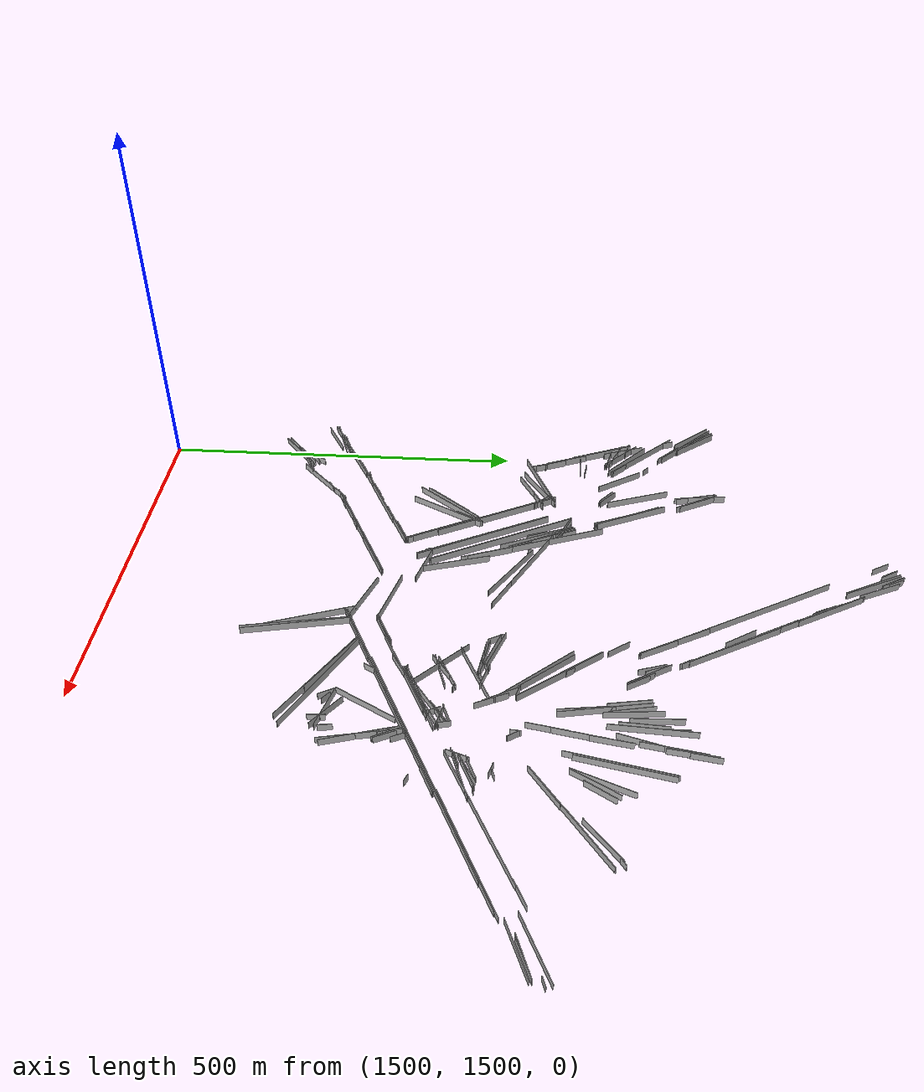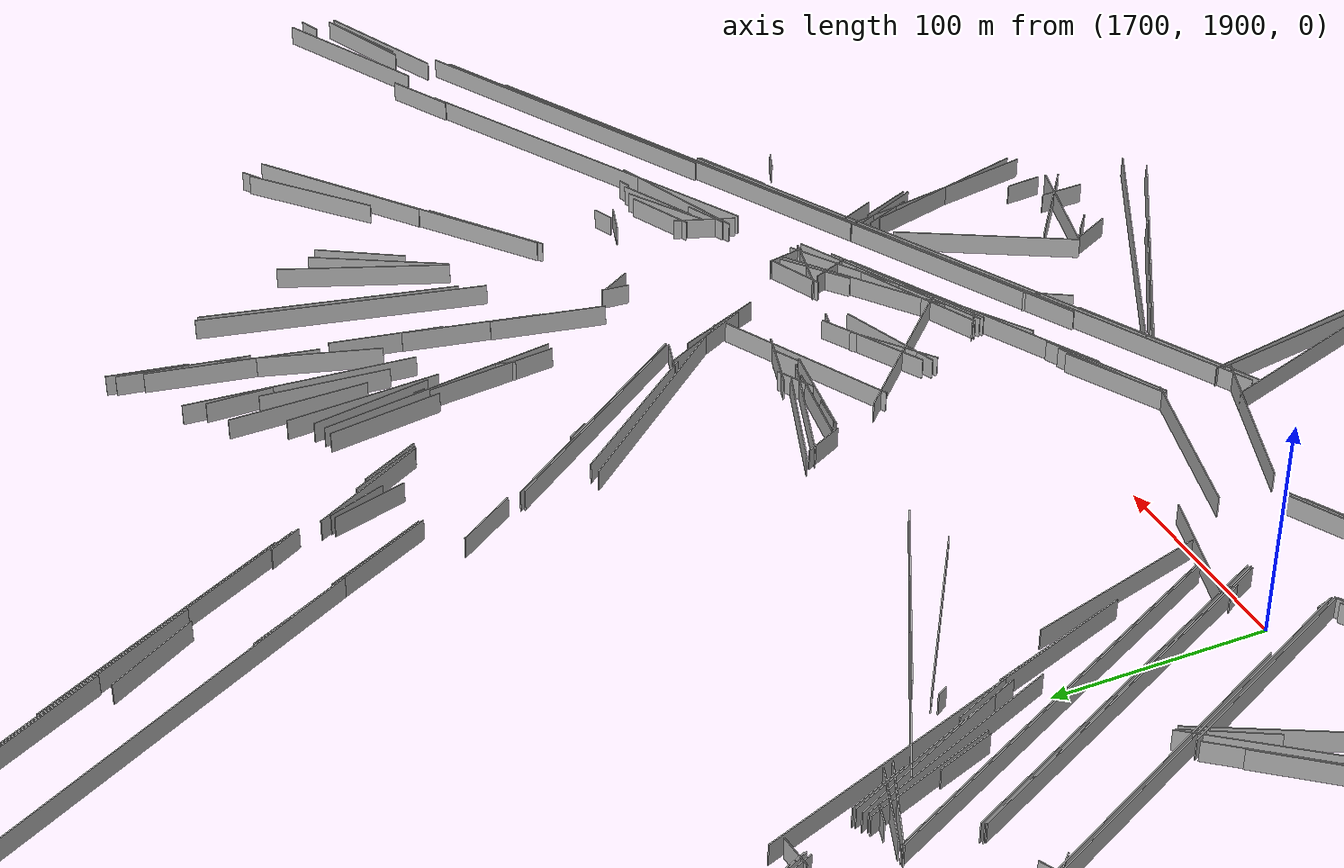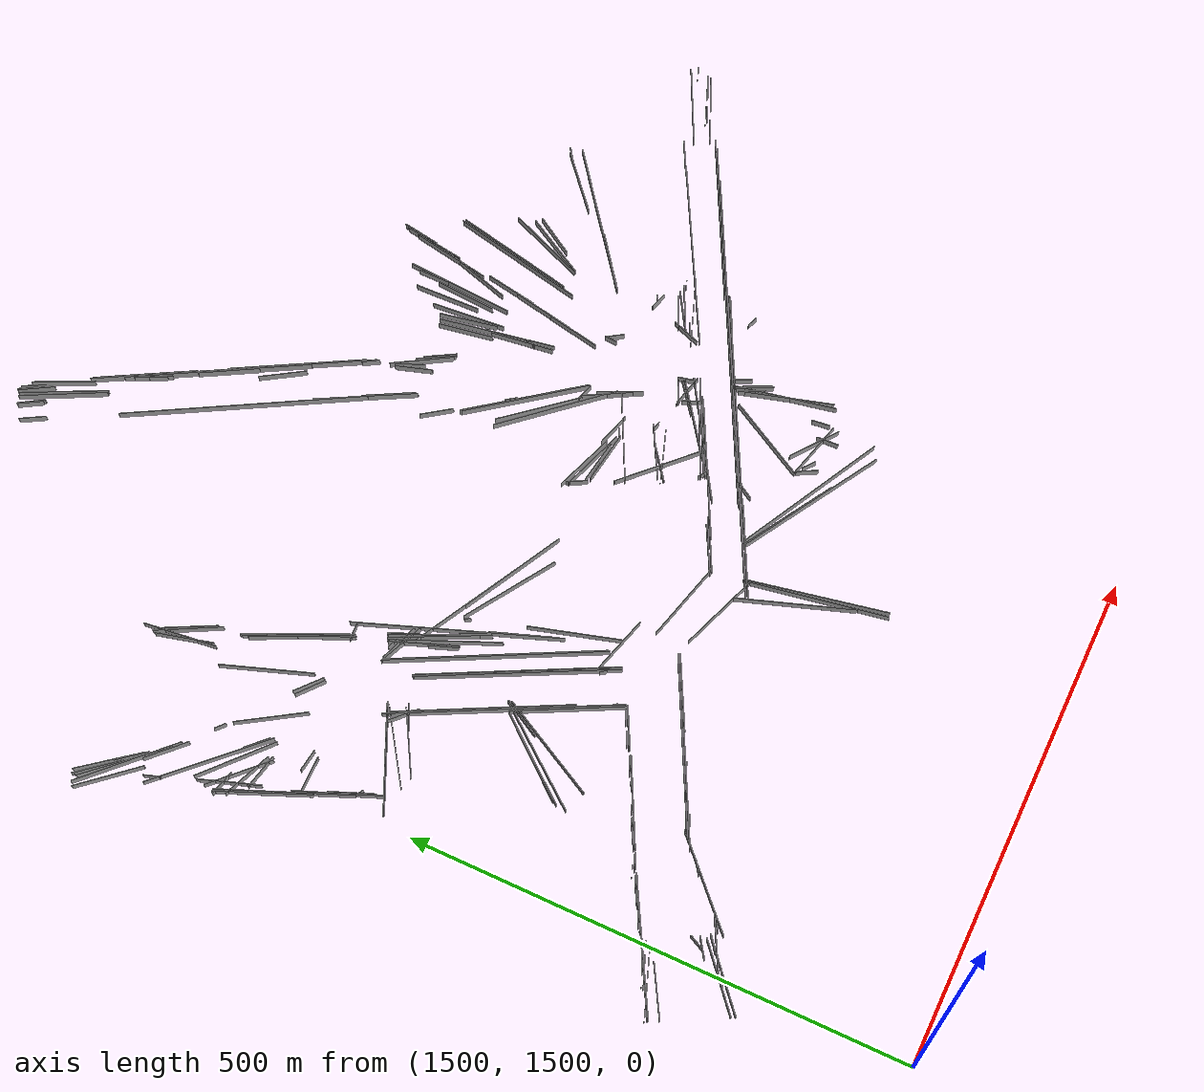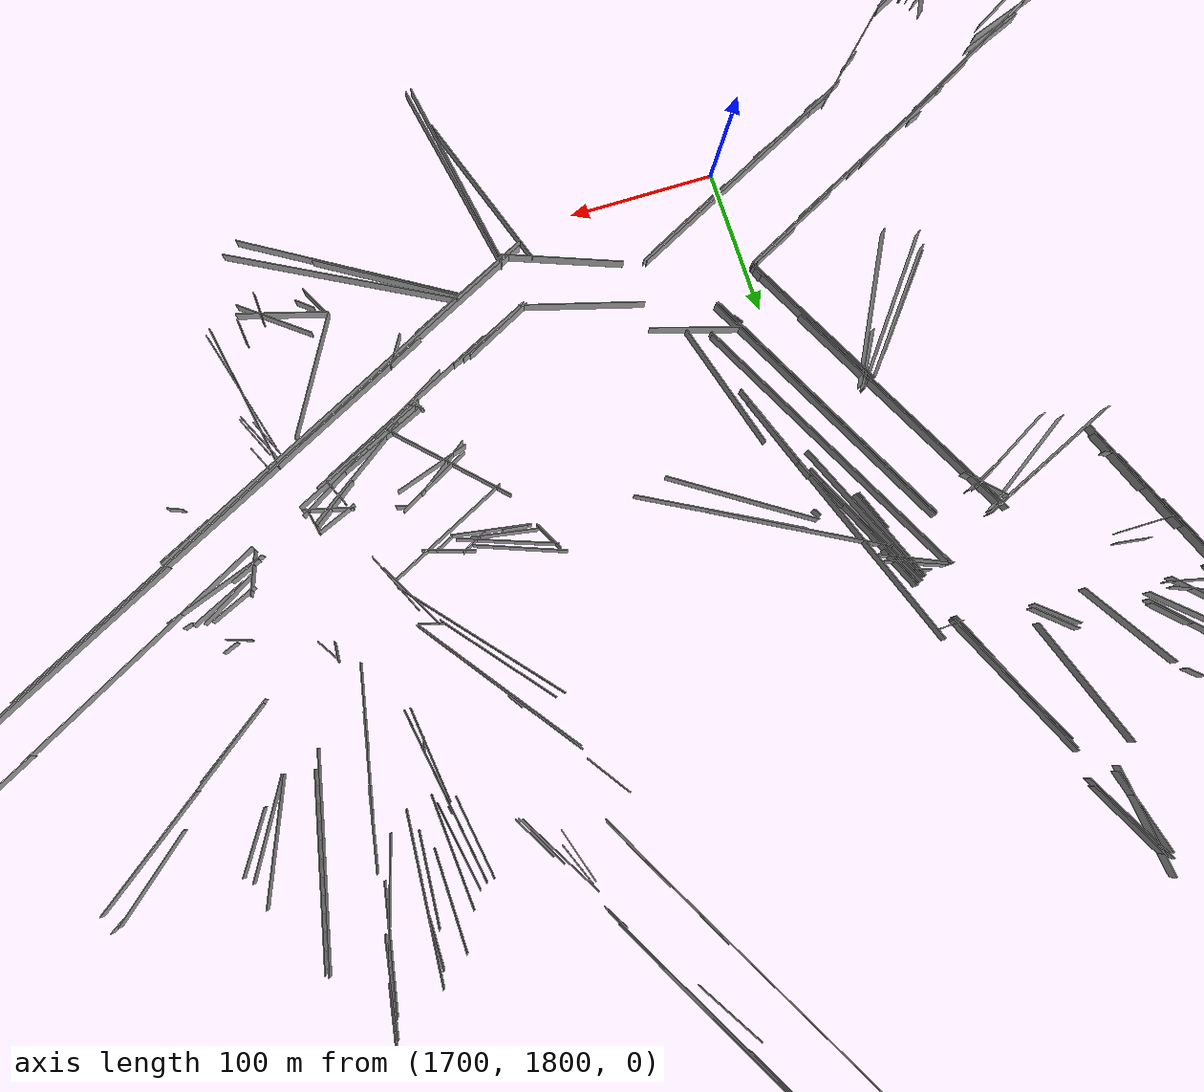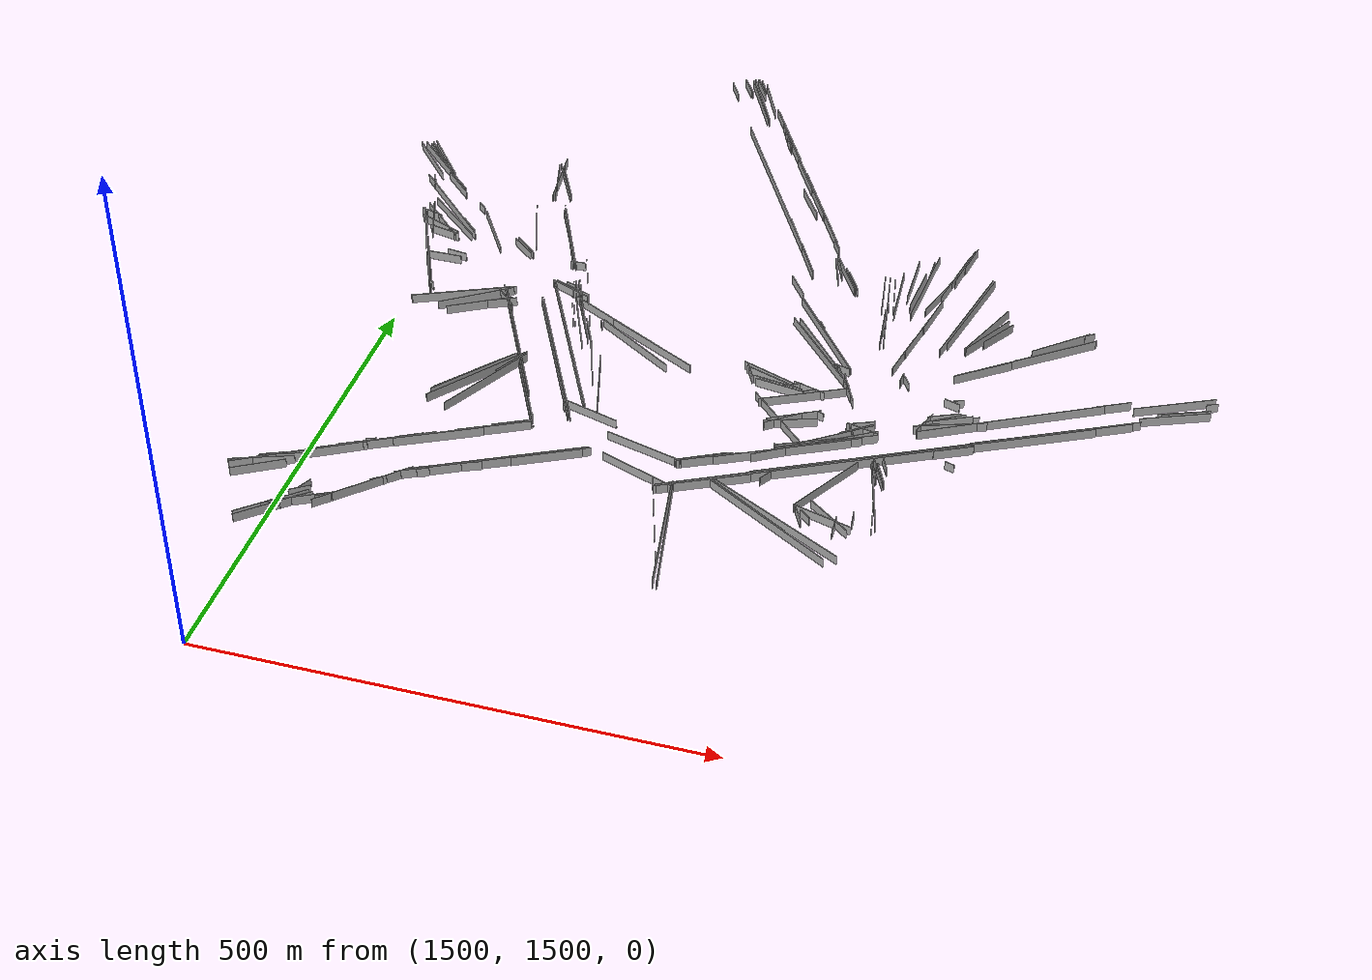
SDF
<?xml version="1.0" encoding="UTF-8" standalone="no"?>
<sdf version="1.6">
  <model name="Worldsegments">
    <static>1</static>
    <pose frame="">0 0 0 0 0 0</pose>
    <link name="Wall_0">
      <pose frame="">2092.0 1943.5 5.0 0 0 0.4706815</pose>
      <collision name="Wall_0_Collision">
        <geometry>
          <box>
            <size>381.48264 0.5 10.0</size>
          </box>
        </geometry>
      </collision>
      <visual name="Wall_0_Visual">
        <geometry>
          <box>
            <size>381.48264 0.5 10.0</size>
          </box>
        </geometry>
      </visual>
    </link>
    <link name="Wall_1">
      <pose frame="">2142.0 2104.0 5.0 0 0 0.6486425</pose>
      <collision name="Wall_1_Collision">
        <geometry>
          <box>
            <size>155.60205 0.5 10.0</size>
          </box>
        </geometry>
      </collision>
      <visual name="Wall_1_Visual">
        <geometry>
          <box>
            <size>155.60205 0.5 10.0</size>
          </box>
        </geometry>
      </visual>
    </link>
    <link name="Wall_2">
      <pose frame="">1846.0 2358.5 5.0 0 0 -1.0668479</pose>
      <collision name="Wall_2_Collision">
        <geometry>
          <box>
            <size>277.49774 0.5 10.0</size>
          </box>
        </geometry>
      </collision>
      <visual name="Wall_2_Visual">
        <geometry>
          <box>
            <size>277.49774 0.5 10.0</size>
          </box>
        </geometry>
      </visual>
    </link>
    <link name="Wall_3">
      <pose frame="">1680.5 1805.0 5.0 0 0 0.47072297</pose>
      <collision name="Wall_3_Collision">
        <geometry>
          <box>
            <size>189.6233 0.5 10.0</size>
          </box>
        </geometry>
      </collision>
      <visual name="Wall_3_Visual">
        <geometry>
          <box>
            <size>189.6233 0.5 10.0</size>
          </box>
        </geometry>
      </visual>
    </link>
    <link name="Wall_4">
      <pose frame="">1684.5 1809.0 5.0 0 0 0.47126168</pose>
      <collision name="Wall_4_Collision">
        <geometry>
          <box>
            <size>176.20726 0.5 10.0</size>
          </box>
        </geometry>
      </collision>
      <visual name="Wall_4_Visual">
        <geometry>
          <box>
            <size>176.20726 0.5 10.0</size>
          </box>
        </geometry>
      </visual>
    </link>
    <link name="Wall_5">
      <pose frame="">1689.5 2003.0 5.0 0 0 -1.0987632</pose>
      <collision name="Wall_5_Collision">
        <geometry>
          <box>
            <size>213.32838 0.5 10.0</size>
          </box>
        </geometry>
      </collision>
      <visual name="Wall_5_Visual">
        <geometry>
          <box>
            <size>213.32838 0.5 10.0</size>
          </box>
        </geometry>
      </visual>
    </link>
    <link name="Wall_6">
      <pose frame="">1601.5 1821.5 5.0 0 0 0.47417355</pose>
      <collision name="Wall_6_Collision">
        <geometry>
          <box>
            <size>212.43823 0.5 10.0</size>
          </box>
        </geometry>
      </collision>
      <visual name="Wall_6_Visual">
        <geometry>
          <box>
            <size>212.43823 0.5 10.0</size>
          </box>
        </geometry>
      </visual>
    </link>
    <link name="Wall_7">
      <pose frame="">1697.0 2046.5 5.0 0 0 -1.2195054</pose>
      <collision name="Wall_7_Collision">
        <geometry>
          <box>
            <size>203.4232 0.5 10.0</size>
          </box>
        </geometry>
      </collision>
      <visual name="Wall_7_Visual">
        <geometry>
          <box>
            <size>203.4232 0.5 10.0</size>
          </box>
        </geometry>
      </visual>
    </link>
    <link name="Wall_8">
      <pose frame="">1878.0 1867.0 5.0 0 0 0.4636476</pose>
      <collision name="Wall_8_Collision">
        <geometry>
          <box>
            <size>62.609905 0.5 10.0</size>
          </box>
        </geometry>
      </collision>
      <visual name="Wall_8_Visual">
        <geometry>
          <box>
            <size>62.609905 0.5 10.0</size>
          </box>
        </geometry>
      </visual>
    </link>
    <link name="Wall_9">
      <pose frame="">1937.5 1901.0 5.0 0 0 -0.5880026</pose>
      <collision name="Wall_9_Collision">
        <geometry>
          <box>
            <size>10.816654 0.5 10.0</size>
          </box>
        </geometry>
      </collision>
      <visual name="Wall_9_Visual">
        <geometry>
          <box>
            <size>10.816654 0.5 10.0</size>
          </box>
        </geometry>
      </visual>
    </link>
    <link name="Wall_10">
      <pose frame="">1816.5 2333.0 5.0 0 0 -1.0624857</pose>
      <collision name="Wall_10_Collision">
        <geometry>
          <box>
            <size>240.39343 0.5 10.0</size>
          </box>
        </geometry>
      </collision>
      <visual name="Wall_10_Visual">
        <geometry>
          <box>
            <size>240.39343 0.5 10.0</size>
          </box>
        </geometry>
      </visual>
    </link>
    <link name="Wall_11">
      <pose frame="">1618.5 1927.5 5.0 0 0 0.90530217</pose>
      <collision name="Wall_11_Collision">
        <geometry>
          <box>
            <size>118.22859 0.5 10.0</size>
          </box>
        </geometry>
      </collision>
      <visual name="Wall_11_Visual">
        <geometry>
          <box>
            <size>118.22859 0.5 10.0</size>
          </box>
        </geometry>
      </visual>
    </link>
    <link name="Wall_12">
      <pose frame="">2146.5 2005.0 5.0 0 0 0.4893429</pose>
      <collision name="Wall_12_Collision">
        <geometry>
          <box>
            <size>191.47063 0.5 10.0</size>
          </box>
        </geometry>
      </collision>
      <visual name="Wall_12_Visual">
        <geometry>
          <box>
            <size>191.47063 0.5 10.0</size>
          </box>
        </geometry>
      </visual>
    </link>
    <link name="Wall_13">
      <pose frame="">2021.0 2076.5 5.0 0 0 1.3843094</pose>
      <collision name="Wall_13_Collision">
        <geometry>
          <box>
            <size>53.935146 0.5 10.0</size>
          </box>
        </geometry>
      </collision>
      <visual name="Wall_13_Visual">
        <geometry>
          <box>
            <size>53.935146 0.5 10.0</size>
          </box>
        </geometry>
      </visual>
    </link>
    <link name="Wall_14">
      <pose frame="">1686.0 2059.0 5.0 0 0 -1.152572</pose>
      <collision name="Wall_14_Collision">
        <geometry>
          <box>
            <size>98.48858 0.5 10.0</size>
          </box>
        </geometry>
      </collision>
      <visual name="Wall_14_Visual">
        <geometry>
          <box>
            <size>98.48858 0.5 10.0</size>
          </box>
        </geometry>
      </visual>
    </link>
    <link name="Wall_15">
      <pose frame="">1683.0 1977.0 5.0 0 0 -1.1025616</pose>
      <collision name="Wall_15_Collision">
        <geometry>
          <box>
            <size>194.98718 0.5 10.0</size>
          </box>
        </geometry>
      </collision>
      <visual name="Wall_15_Visual">
        <geometry>
          <box>
            <size>194.98718 0.5 10.0</size>
          </box>
        </geometry>
      </visual>
    </link>
    <link name="Wall_16">
      <pose frame="">1573.5 1738.0 5.0 0 0 0.76499283</pose>
      <collision name="Wall_16_Collision">
        <geometry>
          <box>
            <size>103.96634 0.5 10.0</size>
          </box>
        </geometry>
      </collision>
      <visual name="Wall_16_Visual">
        <geometry>
          <box>
            <size>103.96634 0.5 10.0</size>
          </box>
        </geometry>
      </visual>
    </link>
    <link name="Wall_17">
      <pose frame="">1955.0 1795.5 5.0 0 0 -0.5393047</pose>
      <collision name="Wall_17_Collision">
        <geometry>
          <box>
            <size>153.83432 0.5 10.0</size>
          </box>
        </geometry>
      </collision>
      <visual name="Wall_17_Visual">
        <geometry>
          <box>
            <size>153.83432 0.5 10.0</size>
          </box>
        </geometry>
      </visual>
    </link>
    <link name="Wall_18">
      <pose frame="">1683.0 2051.5 5.0 0 0 -1.1695676</pose>
      <collision name="Wall_18_Collision">
        <geometry>
          <box>
            <size>107.54069 0.5 10.0</size>
          </box>
        </geometry>
      </collision>
      <visual name="Wall_18_Visual">
        <geometry>
          <box>
            <size>107.54069 0.5 10.0</size>
          </box>
        </geometry>
      </visual>
    </link>
    <link name="Wall_19">
      <pose frame="">1937.0 2088.5 5.0 0 0 -0.92571294</pose>
      <collision name="Wall_19_Collision">
        <geometry>
          <box>
            <size>126.40016 0.5 10.0</size>
          </box>
        </geometry>
      </collision>
      <visual name="Wall_19_Visual">
        <geometry>
          <box>
            <size>126.40016 0.5 10.0</size>
          </box>
        </geometry>
      </visual>
    </link>
    <link name="Wall_20">
      <pose frame="">1754.5 2019.5 5.0 0 0 -0.5743048</pose>
      <collision name="Wall_20_Collision">
        <geometry>
          <box>
            <size>101.24229 0.5 10.0</size>
          </box>
        </geometry>
      </collision>
      <visual name="Wall_20_Visual">
        <geometry>
          <box>
            <size>101.24229 0.5 10.0</size>
          </box>
        </geometry>
      </visual>
    </link>
    <link name="Wall_21">
      <pose frame="">1961.5 1800.5 5.0 0 0 -0.48885235</pose>
      <collision name="Wall_21_Collision">
        <geometry>
          <box>
            <size>159.70598 0.5 10.0</size>
          </box>
        </geometry>
      </collision>
      <visual name="Wall_21_Visual">
        <geometry>
          <box>
            <size>159.70598 0.5 10.0</size>
          </box>
        </geometry>
      </visual>
    </link>
    <link name="Wall_22">
      <pose frame="">1771.0 2024.0 5.0 0 0 -0.48783645</pose>
      <collision name="Wall_22_Collision">
        <geometry>
          <box>
            <size>110.94143 0.5 10.0</size>
          </box>
        </geometry>
      </collision>
      <visual name="Wall_22_Visual">
        <geometry>
          <box>
            <size>110.94143 0.5 10.0</size>
          </box>
        </geometry>
      </visual>
    </link>
    <link name="Wall_23">
      <pose frame="">2192.5 1996.0 5.0 0 0 0.47145995</pose>
      <collision name="Wall_23_Collision">
        <geometry>
          <box>
            <size>171.73526 0.5 10.0</size>
          </box>
        </geometry>
      </collision>
      <visual name="Wall_23_Visual">
        <geometry>
          <box>
            <size>171.73526 0.5 10.0</size>
          </box>
        </geometry>
      </visual>
    </link>
    <link name="Wall_24">
      <pose frame="">2297.0 2072.5 5.0 0 0 0.453066</pose>
      <collision name="Wall_24_Collision">
        <geometry>
          <box>
            <size>84.5281 0.5 10.0</size>
          </box>
        </geometry>
      </collision>
      <visual name="Wall_24_Visual">
        <geometry>
          <box>
            <size>84.5281 0.5 10.0</size>
          </box>
        </geometry>
      </visual>
    </link>
    <link name="Wall_25">
      <pose frame="">1867.0 1751.5 5.0 0 0 -1.3973736</pose>
      <collision name="Wall_25_Collision">
        <geometry>
          <box>
            <size>139.0863 0.5 10.0</size>
          </box>
        </geometry>
      </collision>
      <visual name="Wall_25_Visual">
        <geometry>
          <box>
            <size>139.0863 0.5 10.0</size>
          </box>
        </geometry>
      </visual>
    </link>
    <link name="Wall_26">
      <pose frame="">1615.5 1828.0 5.0 0 0 0.46869808</pose>
      <collision name="Wall_26_Collision">
        <geometry>
          <box>
            <size>88.54942 0.5 10.0</size>
          </box>
        </geometry>
      </collision>
      <visual name="Wall_26_Visual">
        <geometry>
          <box>
            <size>88.54942 0.5 10.0</size>
          </box>
        </geometry>
      </visual>
    </link>
    <link name="Wall_27">
      <pose frame="">2035.0 1913.0 5.0 0 0 0.47186098</pose>
      <collision name="Wall_27_Collision">
        <geometry>
          <box>
            <size>435.60074 0.5 10.0</size>
          </box>
        </geometry>
      </collision>
      <visual name="Wall_27_Visual">
        <geometry>
          <box>
            <size>435.60074 0.5 10.0</size>
          </box>
        </geometry>
      </visual>
    </link>
    <link name="Wall_28">
      <pose frame="">1645.5 1974.0 5.0 0 0 -1.0992594</pose>
      <collision name="Wall_28_Collision">
        <geometry>
          <box>
            <size>226.74435 0.5 10.0</size>
          </box>
        </geometry>
      </collision>
      <visual name="Wall_28_Visual">
        <geometry>
          <box>
            <size>226.74435 0.5 10.0</size>
          </box>
        </geometry>
      </visual>
    </link>
    <link name="Wall_29">
      <pose frame="">1838.0 2371.5 5.0 0 0 -1.0653013</pose>
      <collision name="Wall_29_Collision">
        <geometry>
          <box>
            <size>181.72781 0.5 10.0</size>
          </box>
        </geometry>
      </collision>
      <visual name="Wall_29_Visual">
        <geometry>
          <box>
            <size>181.72781 0.5 10.0</size>
          </box>
        </geometry>
      </visual>
    </link>
    <link name="Wall_30">
      <pose frame="">1719.5 2511.5 5.0 0 0 -1.056345</pose>
      <collision name="Wall_30_Collision">
        <geometry>
          <box>
            <size>26.41969 0.5 10.0</size>
          </box>
        </geometry>
      </collision>
      <visual name="Wall_30_Visual">
        <geometry>
          <box>
            <size>26.41969 0.5 10.0</size>
          </box>
        </geometry>
      </visual>
    </link>
    <link name="Wall_31">
      <pose frame="">1630.5 2181.0 5.0 0 0 -1.1403315</pose>
      <collision name="Wall_31_Collision">
        <geometry>
          <box>
            <size>107.837845 0.5 10.0</size>
          </box>
        </geometry>
      </collision>
      <visual name="Wall_31_Visual">
        <geometry>
          <box>
            <size>107.837845 0.5 10.0</size>
          </box>
        </geometry>
      </visual>
    </link>
    <link name="Wall_32">
      <pose frame="">2043.0 1862.5 5.0 0 0 -1.3790082</pose>
      <collision name="Wall_32_Collision">
        <geometry>
          <box>
            <size>104.92378 0.5 10.0</size>
          </box>
        </geometry>
      </collision>
      <visual name="Wall_32_Visual">
        <geometry>
          <box>
            <size>104.92378 0.5 10.0</size>
          </box>
        </geometry>
      </visual>
    </link>
    <link name="Wall_33">
      <pose frame="">2028.0 2111.5 5.0 0 0 1.3825748</pose>
      <collision name="Wall_33_Collision">
        <geometry>
          <box>
            <size>64.132675 0.5 10.0</size>
          </box>
        </geometry>
      </collision>
      <visual name="Wall_33_Visual">
        <geometry>
          <box>
            <size>64.132675 0.5 10.0</size>
          </box>
        </geometry>
      </visual>
    </link>
    <link name="Wall_34">
      <pose frame="">1943.0 1899.0 5.0 0 0 0.47018346</pose>
      <collision name="Wall_34_Collision">
        <geometry>
          <box>
            <size>136.85028 0.5 10.0</size>
          </box>
        </geometry>
      </collision>
      <visual name="Wall_34_Visual">
        <geometry>
          <box>
            <size>136.85028 0.5 10.0</size>
          </box>
        </geometry>
      </visual>
    </link>
    <link name="Wall_35">
      <pose frame="">1805.5 2433.5 5.0 0 0 -1.0675219</pose>
      <collision name="Wall_35_Collision">
        <geometry>
          <box>
            <size>101.597244 0.5 10.0</size>
          </box>
        </geometry>
      </collision>
      <visual name="Wall_35_Visual">
        <geometry>
          <box>
            <size>101.597244 0.5 10.0</size>
          </box>
        </geometry>
      </visual>
    </link>
    <link name="Wall_36">
      <pose frame="">2035.5 1893.0 5.0 0 0 -1.141034</pose>
      <collision name="Wall_36_Collision">
        <geometry>
          <box>
            <size>26.400757 0.5 10.0</size>
          </box>
        </geometry>
      </collision>
      <visual name="Wall_36_Visual">
        <geometry>
          <box>
            <size>26.400757 0.5 10.0</size>
          </box>
        </geometry>
      </visual>
    </link>
    <link name="Wall_37">
      <pose frame="">1939.5 2186.0 5.0 0 0 -1.0612041</pose>
      <collision name="Wall_37_Collision">
        <geometry>
          <box>
            <size>38.948685 0.5 10.0</size>
          </box>
        </geometry>
      </collision>
      <visual name="Wall_37_Visual">
        <geometry>
          <box>
            <size>38.948685 0.5 10.0</size>
          </box>
        </geometry>
      </visual>
    </link>
    <link name="Wall_38">
      <pose frame="">2035.5 2150.0 5.0 0 0 1.3994172</pose>
      <collision name="Wall_38_Collision">
        <geometry>
          <box>
            <size>52.773098 0.5 10.0</size>
          </box>
        </geometry>
      </collision>
      <visual name="Wall_38_Visual">
        <geometry>
          <box>
            <size>52.773098 0.5 10.0</size>
          </box>
        </geometry>
      </visual>
    </link>
    <link name="Wall_39">
      <pose frame="">2016.5 2197.5 5.0 0 0 1.5054688</pose>
      <collision name="Wall_39_Collision">
        <geometry>
          <box>
            <size>107.22873 0.5 10.0</size>
          </box>
        </geometry>
      </collision>
      <visual name="Wall_39_Visual">
        <geometry>
          <box>
            <size>107.22873 0.5 10.0</size>
          </box>
        </geometry>
      </visual>
    </link>
    <link name="Wall_40">
      <pose frame="">1931.0 2197.0 5.0 0 0 -1.0358412</pose>
      <collision name="Wall_40_Collision">
        <geometry>
          <box>
            <size>62.76942 0.5 10.0</size>
          </box>
        </geometry>
      </collision>
      <visual name="Wall_40_Visual">
        <geometry>
          <box>
            <size>62.76942 0.5 10.0</size>
          </box>
        </geometry>
      </visual>
    </link>
    <link name="Wall_41">
      <pose frame="">2049.5 2241.0 5.0 0 0 1.4219064</pose>
      <collision name="Wall_41_Collision">
        <geometry>
          <box>
            <size>60.671246 0.5 10.0</size>
          </box>
        </geometry>
      </collision>
      <visual name="Wall_41_Visual">
        <geometry>
          <box>
            <size>60.671246 0.5 10.0</size>
          </box>
        </geometry>
      </visual>
    </link>
    <link name="Wall_42">
      <pose frame="">1981.5 2008.5 5.0 0 0 -1.136843</pose>
      <collision name="Wall_42_Collision">
        <geometry>
          <box>
            <size>45.188496 0.5 10.0</size>
          </box>
        </geometry>
      </collision>
      <visual name="Wall_42_Visual">
        <geometry>
          <box>
            <size>45.188496 0.5 10.0</size>
          </box>
        </geometry>
      </visual>
    </link>
    <link name="Wall_43">
      <pose frame="">1499.0 1687.5 5.0 0 0 0.4636476</pose>
      <collision name="Wall_43_Collision">
        <geometry>
          <box>
            <size>20.12461 0.5 10.0</size>
          </box>
        </geometry>
      </collision>
      <visual name="Wall_43_Visual">
        <geometry>
          <box>
            <size>20.12461 0.5 10.0</size>
          </box>
        </geometry>
      </visual>
    </link>
    <link name="Wall_44">
      <pose frame="">1660.0 2096.5 5.0 0 0 -0.2914568</pose>
      <collision name="Wall_44_Collision">
        <geometry>
          <box>
            <size>10.440307 0.5 10.0</size>
          </box>
        </geometry>
      </collision>
      <visual name="Wall_44_Visual">
        <geometry>
          <box>
            <size>10.440307 0.5 10.0</size>
          </box>
        </geometry>
      </visual>
    </link>
    <link name="Wall_45">
      <pose frame="">1557.5 2053.0 5.0 0 0 0.41822433</pose>
      <collision name="Wall_45_Collision">
        <geometry>
          <box>
            <size>108.33743 0.5 10.0</size>
          </box>
        </geometry>
      </collision>
      <visual name="Wall_45_Visual">
        <geometry>
          <box>
            <size>108.33743 0.5 10.0</size>
          </box>
        </geometry>
      </visual>
    </link>
    <link name="Wall_46">
      <pose frame="">1638.5 1991.5 5.0 0 0 -1.0994368</pose>
      <collision name="Wall_46_Collision">
        <geometry>
          <box>
            <size>173.97127 0.5 10.0</size>
          </box>
        </geometry>
      </collision>
      <visual name="Wall_46_Visual">
        <geometry>
          <box>
            <size>173.97127 0.5 10.0</size>
          </box>
        </geometry>
      </visual>
    </link>
    <link name="Wall_47">
      <pose frame="">2018.5 1806.0 5.0 0 0 -1.5253731</pose>
      <collision name="Wall_47_Collision">
        <geometry>
          <box>
            <size>22.022715 0.5 10.0</size>
          </box>
        </geometry>
      </collision>
      <visual name="Wall_47_Visual">
        <geometry>
          <box>
            <size>22.022715 0.5 10.0</size>
          </box>
        </geometry>
      </visual>
    </link>
    <link name="Wall_48">
      <pose frame="">1448.5 2283.5 5.0 0 0 -0.9072406</pose>
      <collision name="Wall_48_Collision">
        <geometry>
          <box>
            <size>69.81404 0.5 10.0</size>
          </box>
        </geometry>
      </collision>
      <visual name="Wall_48_Visual">
        <geometry>
          <box>
            <size>69.81404 0.5 10.0</size>
          </box>
        </geometry>
      </visual>
    </link>
    <link name="Wall_49">
      <pose frame="">1604.0 1824.0 5.0 0 0 0.5070985</pose>
      <collision name="Wall_49_Collision">
        <geometry>
          <box>
            <size>20.59126 0.5 10.0</size>
          </box>
        </geometry>
      </collision>
      <visual name="Wall_49_Visual">
        <geometry>
          <box>
            <size>20.59126 0.5 10.0</size>
          </box>
        </geometry>
      </visual>
    </link>
    <link name="Wall_50">
      <pose frame="">1684.5 1978.5 5.0 0 0 -1.1003151</pose>
      <collision name="Wall_50_Collision">
        <geometry>
          <box>
            <size>196.33136 0.5 10.0</size>
          </box>
        </geometry>
      </collision>
      <visual name="Wall_50_Visual">
        <geometry>
          <box>
            <size>196.33136 0.5 10.0</size>
          </box>
        </geometry>
      </visual>
    </link>
    <link name="Wall_51">
      <pose frame="">1631.0 2176.5 5.0 0 0 -1.1204222</pose>
      <collision name="Wall_51_Collision">
        <geometry>
          <box>
            <size>101.07918 0.5 10.0</size>
          </box>
        </geometry>
      </collision>
      <visual name="Wall_51_Visual">
        <geometry>
          <box>
            <size>101.07918 0.5 10.0</size>
          </box>
        </geometry>
      </visual>
    </link>
    <link name="Wall_52">
      <pose frame="">1498.5 2178.5 5.0 0 0 -0.73372006</pose>
      <collision name="Wall_52_Collision">
        <geometry>
          <box>
            <size>82.13403 0.5 10.0</size>
          </box>
        </geometry>
      </collision>
      <visual name="Wall_52_Visual">
        <geometry>
          <box>
            <size>82.13403 0.5 10.0</size>
          </box>
        </geometry>
      </visual>
    </link>
    <link name="Wall_53">
      <pose frame="">2091.0 1979.5 5.0 0 0 0.35230872</pose>
      <collision name="Wall_53_Collision">
        <geometry>
          <box>
            <size>72.44998 0.5 10.0</size>
          </box>
        </geometry>
      </collision>
      <visual name="Wall_53_Visual">
        <geometry>
          <box>
            <size>72.44998 0.5 10.0</size>
          </box>
        </geometry>
      </visual>
    </link>
    <link name="Wall_54">
      <pose frame="">2002.0 1941.0 5.0 0 0 -1.152572</pose>
      <collision name="Wall_54_Collision">
        <geometry>
          <box>
            <size>19.697716 0.5 10.0</size>
          </box>
        </geometry>
      </collision>
      <visual name="Wall_54_Visual">
        <geometry>
          <box>
            <size>19.697716 0.5 10.0</size>
          </box>
        </geometry>
      </visual>
    </link>
    <link name="Wall_55">
      <pose frame="">1753.5 2496.5 5.0 0 0 -1.1019675</pose>
      <collision name="Wall_55_Collision">
        <geometry>
          <box>
            <size>86.313385 0.5 10.0</size>
          </box>
        </geometry>
      </collision>
      <visual name="Wall_55_Visual">
        <geometry>
          <box>
            <size>86.313385 0.5 10.0</size>
          </box>
        </geometry>
      </visual>
    </link>
    <link name="Wall_56">
      <pose frame="">1435.0 2295.5 5.0 0 0 -0.8794594</pose>
      <collision name="Wall_56_Collision">
        <geometry>
          <box>
            <size>37.64306 0.5 10.0</size>
          </box>
        </geometry>
      </collision>
      <visual name="Wall_56_Visual">
        <geometry>
          <box>
            <size>37.64306 0.5 10.0</size>
          </box>
        </geometry>
      </visual>
    </link>
    <link name="Wall_57">
      <pose frame="">1756.0 2497.0 5.0 0 0 -1.1174576</pose>
      <collision name="Wall_57_Collision">
        <geometry>
          <box>
            <size>86.764046 0.5 10.0</size>
          </box>
        </geometry>
      </collision>
      <visual name="Wall_57_Visual">
        <geometry>
          <box>
            <size>86.764046 0.5 10.0</size>
          </box>
        </geometry>
      </visual>
    </link>
    <link name="Wall_58">
      <pose frame="">2102.0 1944.0 5.0 0 0 0.4636476</pose>
      <collision name="Wall_58_Collision">
        <geometry>
          <box>
            <size>40.24922 0.5 10.0</size>
          </box>
        </geometry>
      </collision>
      <visual name="Wall_58_Visual">
        <geometry>
          <box>
            <size>40.24922 0.5 10.0</size>
          </box>
        </geometry>
      </visual>
    </link>
    <link name="Wall_59">
      <pose frame="">1874.0 2230.0 5.0 0 0 -1.080839</pose>
      <collision name="Wall_59_Collision">
        <geometry>
          <box>
            <size>102.0 0.5 10.0</size>
          </box>
        </geometry>
      </collision>
      <visual name="Wall_59_Visual">
        <geometry>
          <box>
            <size>102.0 0.5 10.0</size>
          </box>
        </geometry>
      </visual>
    </link>
    <link name="Wall_60">
      <pose frame="">1671.0 1920.0 5.0 0 0 -1.0990188</pose>
      <collision name="Wall_60_Collision">
        <geometry>
          <box>
            <size>110.01818 0.5 10.0</size>
          </box>
        </geometry>
      </collision>
      <visual name="Wall_60_Visual">
        <geometry>
          <box>
            <size>110.01818 0.5 10.0</size>
          </box>
        </geometry>
      </visual>
    </link>
    <link name="Wall_61">
      <pose frame="">2300.0 2054.0 5.0 0 0 0.4012288</pose>
      <collision name="Wall_61_Collision">
        <geometry>
          <box>
            <size>71.693794 0.5 10.0</size>
          </box>
        </geometry>
      </collision>
      <visual name="Wall_61_Visual">
        <geometry>
          <box>
            <size>71.693794 0.5 10.0</size>
          </box>
        </geometry>
      </visual>
    </link>
    <link name="Wall_62">
      <pose frame="">1980.0 1882.5 5.0 0 0 0.47218224</pose>
      <collision name="Wall_62_Collision">
        <geometry>
          <box>
            <size>314.40262 0.5 10.0</size>
          </box>
        </geometry>
      </collision>
      <visual name="Wall_62_Visual">
        <geometry>
          <box>
            <size>314.40262 0.5 10.0</size>
          </box>
        </geometry>
      </visual>
    </link>
    <link name="Wall_63">
      <pose frame="">1663.0 2091.0 5.0 0 0 -0.3529904</pose>
      <collision name="Wall_63_Collision">
        <geometry>
          <box>
            <size>40.496914 0.5 10.0</size>
          </box>
        </geometry>
      </collision>
      <visual name="Wall_63_Visual">
        <geometry>
          <box>
            <size>40.496914 0.5 10.0</size>
          </box>
        </geometry>
      </visual>
    </link>
    <link name="Wall_64">
      <pose frame="">1906.0 2003.0 5.0 0 0 -0.34097895</pose>
      <collision name="Wall_64_Collision">
        <geometry>
          <box>
            <size>65.78754 0.5 10.0</size>
          </box>
        </geometry>
      </collision>
      <visual name="Wall_64_Visual">
        <geometry>
          <box>
            <size>65.78754 0.5 10.0</size>
          </box>
        </geometry>
      </visual>
    </link>
    <link name="Wall_65">
      <pose frame="">1996.5 1860.5 5.0 0 0 1.0614952</pose>
      <collision name="Wall_65_Collision">
        <geometry>
          <box>
            <size>88.19297 0.5 10.0</size>
          </box>
        </geometry>
      </collision>
      <visual name="Wall_65_Visual">
        <geometry>
          <box>
            <size>88.19297 0.5 10.0</size>
          </box>
        </geometry>
      </visual>
    </link>
    <link name="Wall_66">
      <pose frame="">1990.0 2117.0 5.0 0 0 -1.442473</pose>
      <collision name="Wall_66_Collision">
        <geometry>
          <box>
            <size>62.514 0.5 10.0</size>
          </box>
        </geometry>
      </collision>
      <visual name="Wall_66_Visual">
        <geometry>
          <box>
            <size>62.514 0.5 10.0</size>
          </box>
        </geometry>
      </visual>
    </link>
    <link name="Wall_67">
      <pose frame="">1871.0 1866.0 5.0 0 0 0.4808873</pose>
      <collision name="Wall_67_Collision">
        <geometry>
          <box>
            <size>51.884487 0.5 10.0</size>
          </box>
        </geometry>
      </collision>
      <visual name="Wall_67_Visual">
        <geometry>
          <box>
            <size>51.884487 0.5 10.0</size>
          </box>
        </geometry>
      </visual>
    </link>
    <link name="Wall_68">
      <pose frame="">1614.0 1929.5 5.0 0 0 0.8928958</pose>
      <collision name="Wall_68_Collision">
        <geometry>
          <box>
            <size>98.85848 0.5 10.0</size>
          </box>
        </geometry>
      </collision>
      <visual name="Wall_68_Visual">
        <geometry>
          <box>
            <size>98.85848 0.5 10.0</size>
          </box>
        </geometry>
      </visual>
    </link>
    <link name="Wall_69">
      <pose frame="">1740.5 1945.5 5.0 0 0 -1.2909793</pose>
      <collision name="Wall_69_Collision">
        <geometry>
          <box>
            <size>90.52071 0.5 10.0</size>
          </box>
        </geometry>
      </collision>
      <visual name="Wall_69_Visual">
        <geometry>
          <box>
            <size>90.52071 0.5 10.0</size>
          </box>
        </geometry>
      </visual>
    </link>
    <link name="Wall_70">
      <pose frame="">1594.0 2277.5 5.0 0 0 -1.0993364</pose>
      <collision name="Wall_70_Collision">
        <geometry>
          <box>
            <size>57.245087 0.5 10.0</size>
          </box>
        </geometry>
      </collision>
      <visual name="Wall_70_Visual">
        <geometry>
          <box>
            <size>57.245087 0.5 10.0</size>
          </box>
        </geometry>
      </visual>
    </link>
    <link name="Wall_71">
      <pose frame="">1993.0 2176.5 5.0 0 0 -1.4887888</pose>
      <collision name="Wall_71_Collision">
        <geometry>
          <box>
            <size>73.24616 0.5 10.0</size>
          </box>
        </geometry>
      </collision>
      <visual name="Wall_71_Visual">
        <geometry>
          <box>
            <size>73.24616 0.5 10.0</size>
          </box>
        </geometry>
      </visual>
    </link>
    <link name="Wall_72">
      <pose frame="">1869.5 1753.5 5.0 0 0 -1.3789408</pose>
      <collision name="Wall_72_Collision">
        <geometry>
          <box>
            <size>141.59802 0.5 10.0</size>
          </box>
        </geometry>
      </collision>
      <visual name="Wall_72_Visual">
        <geometry>
          <box>
            <size>141.59802 0.5 10.0</size>
          </box>
        </geometry>
      </visual>
    </link>
    <link name="Wall_73">
      <pose frame="">1940.0 2058.0 5.0 0 0 -0.8534746</pose>
      <collision name="Wall_73_Collision">
        <geometry>
          <box>
            <size>124.73973 0.5 10.0</size>
          </box>
        </geometry>
      </collision>
      <visual name="Wall_73_Visual">
        <geometry>
          <box>
            <size>124.73973 0.5 10.0</size>
          </box>
        </geometry>
      </visual>
    </link>
    <link name="Wall_74">
      <pose frame="">2033.0 1819.0 5.0 0 0 -1.4601392</pose>
      <collision name="Wall_74_Collision">
        <geometry>
          <box>
            <size>18.110771 0.5 10.0</size>
          </box>
        </geometry>
      </collision>
      <visual name="Wall_74_Visual">
        <geometry>
          <box>
            <size>18.110771 0.5 10.0</size>
          </box>
        </geometry>
      </visual>
    </link>
    <link name="Wall_75">
      <pose frame="">1808.0 2421.0 5.0 0 0 -1.1071488</pose>
      <collision name="Wall_75_Collision">
        <geometry>
          <box>
            <size>17.888544 0.5 10.0</size>
          </box>
        </geometry>
      </collision>
      <visual name="Wall_75_Visual">
        <geometry>
          <box>
            <size>17.888544 0.5 10.0</size>
          </box>
        </geometry>
      </visual>
    </link>
    <link name="Wall_76">
      <pose frame="">1933.0 2072.5 5.0 0 0 -0.87459177</pose>
      <collision name="Wall_76_Collision">
        <geometry>
          <box>
            <size>87.32124 0.5 10.0</size>
          </box>
        </geometry>
      </collision>
      <visual name="Wall_76_Visual">
        <geometry>
          <box>
            <size>87.32124 0.5 10.0</size>
          </box>
        </geometry>
      </visual>
    </link>
    <link name="Wall_77">
      <pose frame="">1842.5 2362.0 5.0 0 0 -1.0620666</pose>
      <collision name="Wall_77_Collision">
        <geometry>
          <box>
            <size>59.5399 0.5 10.0</size>
          </box>
        </geometry>
      </collision>
      <visual name="Wall_77_Visual">
        <geometry>
          <box>
            <size>59.5399 0.5 10.0</size>
          </box>
        </geometry>
      </visual>
    </link>
    <link name="Wall_78">
      <pose frame="">2069.0 2159.0 5.0 0 0 1.3617734</pose>
      <collision name="Wall_78_Collision">
        <geometry>
          <box>
            <size>134.93703 0.5 10.0</size>
          </box>
        </geometry>
      </collision>
      <visual name="Wall_78_Visual">
        <geometry>
          <box>
            <size>134.93703 0.5 10.0</size>
          </box>
        </geometry>
      </visual>
    </link>
    <link name="Wall_79">
      <pose frame="">1725.0 2049.0 5.0 0 0 -0.49394137</pose>
      <collision name="Wall_79_Collision">
        <geometry>
          <box>
            <size>118.11858 0.5 10.0</size>
          </box>
        </geometry>
      </collision>
      <visual name="Wall_79_Visual">
        <geometry>
          <box>
            <size>118.11858 0.5 10.0</size>
          </box>
        </geometry>
      </visual>
    </link>
    <link name="Wall_80">
      <pose frame="">1495.0 1764.0 5.0 0 0 0.50416595</pose>
      <collision name="Wall_80_Collision">
        <geometry>
          <box>
            <size>132.48396 0.5 10.0</size>
          </box>
        </geometry>
      </collision>
      <visual name="Wall_80_Visual">
        <geometry>
          <box>
            <size>132.48396 0.5 10.0</size>
          </box>
        </geometry>
      </visual>
    </link>
    <link name="Wall_81">
      <pose frame="">1981.0 1921.5 5.0 0 0 0.4549142</pose>
      <collision name="Wall_81_Collision">
        <geometry>
          <box>
            <size>102.41582 0.5 10.0</size>
          </box>
        </geometry>
      </collision>
      <visual name="Wall_81_Visual">
        <geometry>
          <box>
            <size>102.41582 0.5 10.0</size>
          </box>
        </geometry>
      </visual>
    </link>
    <link name="Wall_82">
      <pose frame="">1554.5 1798.5 5.0 0 0 0.4717775</pose>
      <collision name="Wall_82_Collision">
        <geometry>
          <box>
            <size>55.00909 0.5 10.0</size>
          </box>
        </geometry>
      </collision>
      <visual name="Wall_82_Visual">
        <geometry>
          <box>
            <size>55.00909 0.5 10.0</size>
          </box>
        </geometry>
      </visual>
    </link>
    <link name="Wall_83">
      <pose frame="">1930.5 2101.0 5.0 0 0 -0.9600704</pose>
      <collision name="Wall_83_Collision">
        <geometry>
          <box>
            <size>12.206555 0.5 10.0</size>
          </box>
        </geometry>
      </collision>
      <visual name="Wall_83_Visual">
        <geometry>
          <box>
            <size>12.206555 0.5 10.0</size>
          </box>
        </geometry>
      </visual>
    </link>
    <link name="Wall_84">
      <pose frame="">2005.0 1814.0 5.0 0 0 -0.26916748</pose>
      <collision name="Wall_84_Collision">
        <geometry>
          <box>
            <size>60.166435 0.5 10.0</size>
          </box>
        </geometry>
      </collision>
      <visual name="Wall_84_Visual">
        <geometry>
          <box>
            <size>60.166435 0.5 10.0</size>
          </box>
        </geometry>
      </visual>
    </link>
    <link name="Wall_85">
      <pose frame="">1489.0 2123.5 5.0 0 0 -1.1846956</pose>
      <collision name="Wall_85_Collision">
        <geometry>
          <box>
            <size>132.77425 0.5 10.0</size>
          </box>
        </geometry>
      </collision>
      <visual name="Wall_85_Visual">
        <geometry>
          <box>
            <size>132.77425 0.5 10.0</size>
          </box>
        </geometry>
      </visual>
    </link>
    <link name="Wall_86">
      <pose frame="">1525.0 1704.0 5.0 0 0 0.47835243</pose>
      <collision name="Wall_86_Collision">
        <geometry>
          <box>
            <size>60.827625 0.5 10.0</size>
          </box>
        </geometry>
      </collision>
      <visual name="Wall_86_Visual">
        <geometry>
          <box>
            <size>60.827625 0.5 10.0</size>
          </box>
        </geometry>
      </visual>
    </link>
    <link name="Wall_87">
      <pose frame="">2021.0 1955.0 5.0 0 0 -1.3521274</pose>
      <collision name="Wall_87_Collision">
        <geometry>
          <box>
            <size>18.439089 0.5 10.0</size>
          </box>
        </geometry>
      </collision>
      <visual name="Wall_87_Visual">
        <geometry>
          <box>
            <size>18.439089 0.5 10.0</size>
          </box>
        </geometry>
      </visual>
    </link>
    <link name="Wall_88">
      <pose frame="">1690.0 2004.0 5.0 0 0 -1.0986743</pose>
      <collision name="Wall_88_Collision">
        <geometry>
          <box>
            <size>211.09239 0.5 10.0</size>
          </box>
        </geometry>
      </collision>
      <visual name="Wall_88_Visual">
        <geometry>
          <box>
            <size>211.09239 0.5 10.0</size>
          </box>
        </geometry>
      </visual>
    </link>
    <link name="Wall_89">
      <pose frame="">1520.5 2167.5 5.0 0 0 -0.7853982</pose>
      <collision name="Wall_89_Collision">
        <geometry>
          <box>
            <size>26.870058 0.5 10.0</size>
          </box>
        </geometry>
      </collision>
      <visual name="Wall_89_Visual">
        <geometry>
          <box>
            <size>26.870058 0.5 10.0</size>
          </box>
        </geometry>
      </visual>
    </link>
    <link name="Wall_90">
      <pose frame="">1645.0 1955.0 5.0 0 0 1.0636978</pose>
      <collision name="Wall_90_Collision">
        <geometry>
          <box>
            <size>41.18252 0.5 10.0</size>
          </box>
        </geometry>
      </collision>
      <visual name="Wall_90_Visual">
        <geometry>
          <box>
            <size>41.18252 0.5 10.0</size>
          </box>
        </geometry>
      </visual>
    </link>
    <link name="Wall_91">
      <pose frame="">2070.0 1973.5 5.0 0 0 0.42285392</pose>
      <collision name="Wall_91_Collision">
        <geometry>
          <box>
            <size>21.931713 0.5 10.0</size>
          </box>
        </geometry>
      </collision>
      <visual name="Wall_91_Visual">
        <geometry>
          <box>
            <size>21.931713 0.5 10.0</size>
          </box>
        </geometry>
      </visual>
    </link>
    <link name="Wall_92">
      <pose frame="">1718.0 1905.0 5.0 0 0 -0.98279375</pose>
      <collision name="Wall_92_Collision">
        <geometry>
          <box>
            <size>7.2111025 0.5 10.0</size>
          </box>
        </geometry>
      </collision>
      <visual name="Wall_92_Visual">
        <geometry>
          <box>
            <size>7.2111025 0.5 10.0</size>
          </box>
        </geometry>
      </visual>
    </link>
    <link name="Wall_93">
      <pose frame="">1465.5 1736.5 5.0 0 0 0.5214344</pose>
      <collision name="Wall_93_Collision">
        <geometry>
          <box>
            <size>54.20332 0.5 10.0</size>
          </box>
        </geometry>
      </collision>
      <visual name="Wall_93_Visual">
        <geometry>
          <box>
            <size>54.20332 0.5 10.0</size>
          </box>
        </geometry>
      </visual>
    </link>
    <link name="Wall_94">
      <pose frame="">2044.0 1857.0 5.0 0 0 -1.2924967</pose>
      <collision name="Wall_94_Collision">
        <geometry>
          <box>
            <size>87.36132 0.5 10.0</size>
          </box>
        </geometry>
      </collision>
      <visual name="Wall_94_Visual">
        <geometry>
          <box>
            <size>87.36132 0.5 10.0</size>
          </box>
        </geometry>
      </visual>
    </link>
    <link name="Wall_95">
      <pose frame="">1662.0 2088.5 5.0 0 0 -0.40763152</pose>
      <collision name="Wall_95_Collision">
        <geometry>
          <box>
            <size>47.92703 0.5 10.0</size>
          </box>
        </geometry>
      </collision>
      <visual name="Wall_95_Visual">
        <geometry>
          <box>
            <size>47.92703 0.5 10.0</size>
          </box>
        </geometry>
      </visual>
    </link>
    <link name="Wall_96">
      <pose frame="">2053.0 2256.5 5.0 0 0 1.4100336</pose>
      <collision name="Wall_96_Collision">
        <geometry>
          <box>
            <size>37.48333 0.5 10.0</size>
          </box>
        </geometry>
      </collision>
      <visual name="Wall_96_Visual">
        <geometry>
          <box>
            <size>37.48333 0.5 10.0</size>
          </box>
        </geometry>
      </visual>
    </link>
    <link name="Wall_97">
      <pose frame="">2239.5 2055.0 5.0 0 0 0.47646743</pose>
      <collision name="Wall_97_Collision">
        <geometry>
          <box>
            <size>34.88553 0.5 10.0</size>
          </box>
        </geometry>
      </collision>
      <visual name="Wall_97_Visual">
        <geometry>
          <box>
            <size>34.88553 0.5 10.0</size>
          </box>
        </geometry>
      </visual>
    </link>
    <link name="Wall_98">
      <pose frame="">2094.0 2139.5 5.0 0 0 1.19029</pose>
      <collision name="Wall_98_Collision">
        <geometry>
          <box>
            <size>80.77747 0.5 10.0</size>
          </box>
        </geometry>
      </collision>
      <visual name="Wall_98_Visual">
        <geometry>
          <box>
            <size>80.77747 0.5 10.0</size>
          </box>
        </geometry>
      </visual>
    </link>
    <link name="Wall_99">
      <pose frame="">1508.5 2078.5 5.0 0 0 -1.1968544</pose>
      <collision name="Wall_99_Collision">
        <geometry>
          <box>
            <size>84.8646 0.5 10.0</size>
          </box>
        </geometry>
      </collision>
      <visual name="Wall_99_Visual">
        <geometry>
          <box>
            <size>84.8646 0.5 10.0</size>
          </box>
        </geometry>
      </visual>
    </link>
    <link name="Wall_100">
      <pose frame="">2332.5 2082.0 5.0 0 0 0.348771</pose>
      <collision name="Wall_100_Collision">
        <geometry>
          <box>
            <size>11.7046995 0.5 10.0</size>
          </box>
        </geometry>
      </collision>
      <visual name="Wall_100_Visual">
        <geometry>
          <box>
            <size>11.7046995 0.5 10.0</size>
          </box>
        </geometry>
      </visual>
    </link>
    <link name="Wall_101">
      <pose frame="">1884.5 1872.0 5.0 0 0 0.4497596</pose>
      <collision name="Wall_101_Collision">
        <geometry>
          <box>
            <size>32.202484 0.5 10.0</size>
          </box>
        </geometry>
      </collision>
      <visual name="Wall_101_Visual">
        <geometry>
          <box>
            <size>32.202484 0.5 10.0</size>
          </box>
        </geometry>
      </visual>
    </link>
    <link name="Wall_102">
      <pose frame="">1965.0 1916.5 5.0 0 0 0.43750978</pose>
      <collision name="Wall_102_Collision">
        <geometry>
          <box>
            <size>68.44706 0.5 10.0</size>
          </box>
        </geometry>
      </collision>
      <visual name="Wall_102_Visual">
        <geometry>
          <box>
            <size>68.44706 0.5 10.0</size>
          </box>
        </geometry>
      </visual>
    </link>
    <link name="Wall_103">
      <pose frame="">2002.0 2203.5 5.0 0 0 -1.5400368</pose>
      <collision name="Wall_103_Collision">
        <geometry>
          <box>
            <size>65.03076 0.5 10.0</size>
          </box>
        </geometry>
      </collision>
      <visual name="Wall_103_Visual">
        <geometry>
          <box>
            <size>65.03076 0.5 10.0</size>
          </box>
        </geometry>
      </visual>
    </link>
    <link name="Wall_104">
      <pose frame="">1518.0 1715.0 5.0 0 0 0.5880026</pose>
      <collision name="Wall_104_Collision">
        <geometry>
          <box>
            <size>21.633308 0.5 10.0</size>
          </box>
        </geometry>
      </collision>
      <visual name="Wall_104_Visual">
        <geometry>
          <box>
            <size>21.633308 0.5 10.0</size>
          </box>
        </geometry>
      </visual>
    </link>
    <link name="Wall_105">
      <pose frame="">1588.0 2192.0 5.0 0 0 -1.2351577</pose>
      <collision name="Wall_105_Collision">
        <geometry>
          <box>
            <size>91.08238 0.5 10.0</size>
          </box>
        </geometry>
      </collision>
      <visual name="Wall_105_Visual">
        <geometry>
          <box>
            <size>91.08238 0.5 10.0</size>
          </box>
        </geometry>
      </visual>
    </link>
    <link name="Wall_106">
      <pose frame="">1502.5 1687.5 5.0 0 0 0.7127987</pose>
      <collision name="Wall_106_Collision">
        <geometry>
          <box>
            <size>77.987175 0.5 10.0</size>
          </box>
        </geometry>
      </collision>
      <visual name="Wall_106_Visual">
        <geometry>
          <box>
            <size>77.987175 0.5 10.0</size>
          </box>
        </geometry>
      </visual>
    </link>
    <link name="Wall_107">
      <pose frame="">2044.0 2220.0 5.0 0 0 1.3932002</pose>
      <collision name="Wall_107_Collision">
        <geometry>
          <box>
            <size>79.24645 0.5 10.0</size>
          </box>
        </geometry>
      </collision>
      <visual name="Wall_107_Visual">
        <geometry>
          <box>
            <size>79.24645 0.5 10.0</size>
          </box>
        </geometry>
      </visual>
    </link>
    <link name="Wall_108">
      <pose frame="">1548.0 2167.0 5.0 0 0 -1.0062269</pose>
      <collision name="Wall_108_Collision">
        <geometry>
          <box>
            <size>71.021126 0.5 10.0</size>
          </box>
        </geometry>
      </collision>
      <visual name="Wall_108_Visual">
        <geometry>
          <box>
            <size>71.021126 0.5 10.0</size>
          </box>
        </geometry>
      </visual>
    </link>
    <link name="Wall_109">
      <pose frame="">1630.0 1922.0 5.0 0 0 1.0829599</pose>
      <collision name="Wall_109_Collision">
        <geometry>
          <box>
            <size>110.94143 0.5 10.0</size>
          </box>
        </geometry>
      </collision>
      <visual name="Wall_109_Visual">
        <geometry>
          <box>
            <size>110.94143 0.5 10.0</size>
          </box>
        </geometry>
      </visual>
    </link>
    <link name="Wall_110">
      <pose frame="">2170.5 2139.0 5.0 0 0 0.7118469</pose>
      <collision name="Wall_110_Collision">
        <geometry>
          <box>
            <size>67.357254 0.5 10.0</size>
          </box>
        </geometry>
      </collision>
      <visual name="Wall_110_Visual">
        <geometry>
          <box>
            <size>67.357254 0.5 10.0</size>
          </box>
        </geometry>
      </visual>
    </link>
    <link name="Wall_111">
      <pose frame="">1806.5 2425.5 5.0 0 0 -1.0951011</pose>
      <collision name="Wall_111_Collision">
        <geometry>
          <box>
            <size>37.12142 0.5 10.0</size>
          </box>
        </geometry>
      </collision>
      <visual name="Wall_111_Visual">
        <geometry>
          <box>
            <size>37.12142 0.5 10.0</size>
          </box>
        </geometry>
      </visual>
    </link>
    <link name="Wall_112">
      <pose frame="">1888.5 2160.5 5.0 0 0 -0.957589</pose>
      <collision name="Wall_112_Collision">
        <geometry>
          <box>
            <size>33.01515 0.5 10.0</size>
          </box>
        </geometry>
      </collision>
      <visual name="Wall_112_Visual">
        <geometry>
          <box>
            <size>33.01515 0.5 10.0</size>
          </box>
        </geometry>
      </visual>
    </link>
    <link name="Wall_113">
      <pose frame="">1489.0 2162.0 5.0 0 0 -0.39479113</pose>
      <collision name="Wall_113_Collision">
        <geometry>
          <box>
            <size>52.0 0.5 10.0</size>
          </box>
        </geometry>
      </collision>
      <visual name="Wall_113_Visual">
        <geometry>
          <box>
            <size>52.0 0.5 10.0</size>
          </box>
        </geometry>
      </visual>
    </link>
    <link name="Wall_114">
      <pose frame="">1556.0 1802.0 5.0 0 0 0.38050637</pose>
      <collision name="Wall_114_Collision">
        <geometry>
          <box>
            <size>10.770329 0.5 10.0</size>
          </box>
        </geometry>
      </collision>
      <visual name="Wall_114_Visual">
        <geometry>
          <box>
            <size>10.770329 0.5 10.0</size>
          </box>
        </geometry>
      </visual>
    </link>
    <link name="Wall_115">
      <pose frame="">1487.0 2200.5 5.0 0 0 -0.8021564</pose>
      <collision name="Wall_115_Collision">
        <geometry>
          <box>
            <size>126.58989 0.5 10.0</size>
          </box>
        </geometry>
      </collision>
      <visual name="Wall_115_Visual">
        <geometry>
          <box>
            <size>126.58989 0.5 10.0</size>
          </box>
        </geometry>
      </visual>
    </link>
    <link name="Wall_116">
      <pose frame="">2033.5 2037.0 5.0 0 0 -0.99945885</pose>
      <collision name="Wall_116_Collision">
        <geometry>
          <box>
            <size>16.643316 0.5 10.0</size>
          </box>
        </geometry>
      </collision>
      <visual name="Wall_116_Visual">
        <geometry>
          <box>
            <size>16.643316 0.5 10.0</size>
          </box>
        </geometry>
      </visual>
    </link>
    <link name="Wall_117">
      <pose frame="">1520.5 2206.0 5.0 0 0 -0.7266424</pose>
      <collision name="Wall_117_Collision">
        <geometry>
          <box>
            <size>12.0415945 0.5 10.0</size>
          </box>
        </geometry>
      </collision>
      <visual name="Wall_117_Visual">
        <geometry>
          <box>
            <size>12.0415945 0.5 10.0</size>
          </box>
        </geometry>
      </visual>
    </link>
    <link name="Wall_118">
      <pose frame="">1992.0 2109.5 5.0 0 0 1.3521274</pose>
      <collision name="Wall_118_Collision">
        <geometry>
          <box>
            <size>9.219544 0.5 10.0</size>
          </box>
        </geometry>
      </collision>
      <visual name="Wall_118_Visual">
        <geometry>
          <box>
            <size>9.219544 0.5 10.0</size>
          </box>
        </geometry>
      </visual>
    </link>
    <link name="Wall_119">
      <pose frame="">1439.0 2290.0 5.0 0 0 -0.87605804</pose>
      <collision name="Wall_119_Collision">
        <geometry>
          <box>
            <size>46.8615 0.5 10.0</size>
          </box>
        </geometry>
      </collision>
      <visual name="Wall_119_Visual">
        <geometry>
          <box>
            <size>46.8615 0.5 10.0</size>
          </box>
        </geometry>
      </visual>
    </link>
    <link name="Wall_120">
      <pose frame="">1683.5 1977.5 5.0 0 0 -1.1003151</pose>
      <collision name="Wall_120_Collision">
        <geometry>
          <box>
            <size>196.33136 0.5 10.0</size>
          </box>
        </geometry>
      </collision>
      <visual name="Wall_120_Visual">
        <geometry>
          <box>
            <size>196.33136 0.5 10.0</size>
          </box>
        </geometry>
      </visual>
    </link>
    <link name="Wall_121">
      <pose frame="">1434.5 2278.0 5.0 0 0 -0.8574382</pose>
      <collision name="Wall_121_Collision">
        <geometry>
          <box>
            <size>68.76772 0.5 10.0</size>
          </box>
        </geometry>
      </collision>
      <visual name="Wall_121_Visual">
        <geometry>
          <box>
            <size>68.76772 0.5 10.0</size>
          </box>
        </geometry>
      </visual>
    </link>
    <link name="Wall_122">
      <pose frame="">1601.5 2056.5 5.0 0 0 -0.7853982</pose>
      <collision name="Wall_122_Collision">
        <geometry>
          <box>
            <size>32.526913 0.5 10.0</size>
          </box>
        </geometry>
      </collision>
      <visual name="Wall_122_Visual">
        <geometry>
          <box>
            <size>32.526913 0.5 10.0</size>
          </box>
        </geometry>
      </visual>
    </link>
    <link name="Wall_123">
      <pose frame="">1749.5 2526.5 5.0 0 0 -1.0882831</pose>
      <collision name="Wall_123_Collision">
        <geometry>
          <box>
            <size>23.70654 0.5 10.0</size>
          </box>
        </geometry>
      </collision>
      <visual name="Wall_123_Visual">
        <geometry>
          <box>
            <size>23.70654 0.5 10.0</size>
          </box>
        </geometry>
      </visual>
    </link>
    <link name="Wall_124">
      <pose frame="">1988.5 2174.5 5.0 0 0 -1.3801575</pose>
      <collision name="Wall_124_Collision">
        <geometry>
          <box>
            <size>58.0517 0.5 10.0</size>
          </box>
        </geometry>
      </collision>
      <visual name="Wall_124_Visual">
        <geometry>
          <box>
            <size>58.0517 0.5 10.0</size>
          </box>
        </geometry>
      </visual>
    </link>
    <link name="Wall_125">
      <pose frame="">1899.5 2009.5 5.0 0 0 -0.3529904</pose>
      <collision name="Wall_125_Collision">
        <geometry>
          <box>
            <size>60.74537 0.5 10.0</size>
          </box>
        </geometry>
      </collision>
      <visual name="Wall_125_Visual">
        <geometry>
          <box>
            <size>60.74537 0.5 10.0</size>
          </box>
        </geometry>
      </visual>
    </link>
    <link name="Wall_126">
      <pose frame="">1584.5 1749.5 5.0 0 0 0.6055447</pose>
      <collision name="Wall_126_Collision">
        <geometry>
          <box>
            <size>15.811388 0.5 10.0</size>
          </box>
        </geometry>
      </collision>
      <visual name="Wall_126_Visual">
        <geometry>
          <box>
            <size>15.811388 0.5 10.0</size>
          </box>
        </geometry>
      </visual>
    </link>
    <link name="Wall_127">
      <pose frame="">1499.5 1690.5 5.0 0 0 0.7100693</pose>
      <collision name="Wall_127_Collision">
        <geometry>
          <box>
            <size>75.16648 0.5 10.0</size>
          </box>
        </geometry>
      </collision>
      <visual name="Wall_127_Visual">
        <geometry>
          <box>
            <size>75.16648 0.5 10.0</size>
          </box>
        </geometry>
      </visual>
    </link>
    <link name="Wall_128">
      <pose frame="">1940.0 1986.0 5.0 0 0 0.4636476</pose>
      <collision name="Wall_128_Collision">
        <geometry>
          <box>
            <size>89.44272 0.5 10.0</size>
          </box>
        </geometry>
      </collision>
      <visual name="Wall_128_Visual">
        <geometry>
          <box>
            <size>89.44272 0.5 10.0</size>
          </box>
        </geometry>
      </visual>
    </link>
    <link name="Wall_129">
      <pose frame="">2043.0 1905.5 5.0 0 0 -1.1309538</pose>
      <collision name="Wall_129_Collision">
        <geometry>
          <box>
            <size>18.788294 0.5 10.0</size>
          </box>
        </geometry>
      </collision>
      <visual name="Wall_129_Visual">
        <geometry>
          <box>
            <size>18.788294 0.5 10.0</size>
          </box>
        </geometry>
      </visual>
    </link>
    <link name="Wall_130">
      <pose frame="">1591.0 2149.5 5.0 0 0 -0.71883</pose>
      <collision name="Wall_130_Collision">
        <geometry>
          <box>
            <size>31.890438 0.5 10.0</size>
          </box>
        </geometry>
      </collision>
      <visual name="Wall_130_Visual">
        <geometry>
          <box>
            <size>31.890438 0.5 10.0</size>
          </box>
        </geometry>
      </visual>
    </link>
    <link name="Wall_131">
      <pose frame="">1609.5 1925.0 5.0 0 0 0.88597506</pose>
      <collision name="Wall_131_Collision">
        <geometry>
          <box>
            <size>77.46612 0.5 10.0</size>
          </box>
        </geometry>
      </collision>
      <visual name="Wall_131_Visual">
        <geometry>
          <box>
            <size>77.46612 0.5 10.0</size>
          </box>
        </geometry>
      </visual>
    </link>
    <link name="Wall_132">
      <pose frame="">1465.0 1746.0 5.0 0 0 0.35144478</pose>
      <collision name="Wall_132_Collision">
        <geometry>
          <box>
            <size>63.90618 0.5 10.0</size>
          </box>
        </geometry>
      </collision>
      <visual name="Wall_132_Visual">
        <geometry>
          <box>
            <size>63.90618 0.5 10.0</size>
          </box>
        </geometry>
      </visual>
    </link>
    <link name="Wall_133">
      <pose frame="">2040.0 1891.5 5.0 0 0 -1.1193433</pose>
      <collision name="Wall_133_Collision">
        <geometry>
          <box>
            <size>36.67424 0.5 10.0</size>
          </box>
        </geometry>
      </collision>
      <visual name="Wall_133_Visual">
        <geometry>
          <box>
            <size>36.67424 0.5 10.0</size>
          </box>
        </geometry>
      </visual>
    </link>
    <link name="Wall_134">
      <pose frame="">1765.0 2502.0 5.0 0 0 -1.1361262</pose>
      <collision name="Wall_134_Collision">
        <geometry>
          <box>
            <size>61.741398 0.5 10.0</size>
          </box>
        </geometry>
      </collision>
      <visual name="Wall_134_Visual">
        <geometry>
          <box>
            <size>61.741398 0.5 10.0</size>
          </box>
        </geometry>
      </visual>
    </link>
    <link name="Wall_135">
      <pose frame="">1663.0 1854.0 5.0 0 0 0.4636476</pose>
      <collision name="Wall_135_Collision">
        <geometry>
          <box>
            <size>76.02631 0.5 10.0</size>
          </box>
        </geometry>
      </collision>
      <visual name="Wall_135_Visual">
        <geometry>
          <box>
            <size>76.02631 0.5 10.0</size>
          </box>
        </geometry>
      </visual>
    </link>
    <link name="Wall_136">
      <pose frame="">1932.5 1945.0 5.0 0 0 0.638914</pose>
      <collision name="Wall_136_Collision">
        <geometry>
          <box>
            <size>43.60046 0.5 10.0</size>
          </box>
        </geometry>
      </collision>
      <visual name="Wall_136_Visual">
        <geometry>
          <box>
            <size>43.60046 0.5 10.0</size>
          </box>
        </geometry>
      </visual>
    </link>
    <link name="Wall_137">
      <pose frame="">1971.0 1881.0 5.0 0 0 0.47249693</pose>
      <collision name="Wall_137_Collision">
        <geometry>
          <box>
            <size>101.07423 0.5 10.0</size>
          </box>
        </geometry>
      </collision>
      <visual name="Wall_137_Visual">
        <geometry>
          <box>
            <size>101.07423 0.5 10.0</size>
          </box>
        </geometry>
      </visual>
    </link>
    <link name="Wall_138">
      <pose frame="">1988.0 2143.0 5.0 0 0 -1.3971251</pose>
      <collision name="Wall_138_Collision">
        <geometry>
          <box>
            <size>115.74109 0.5 10.0</size>
          </box>
        </geometry>
      </collision>
      <visual name="Wall_138_Visual">
        <geometry>
          <box>
            <size>115.74109 0.5 10.0</size>
          </box>
        </geometry>
      </visual>
    </link>
    <link name="Wall_139">
      <pose frame="">1590.0 1817.5 5.0 0 0 0.49642277</pose>
      <collision name="Wall_139_Collision">
        <geometry>
          <box>
            <size>27.294687 0.5 10.0</size>
          </box>
        </geometry>
      </collision>
      <visual name="Wall_139_Visual">
        <geometry>
          <box>
            <size>27.294687 0.5 10.0</size>
          </box>
        </geometry>
      </visual>
    </link>
    <link name="Wall_140">
      <pose frame="">1476.0 2174.5 5.0 0 0 -1.2333403</pose>
      <collision name="Wall_140_Collision">
        <geometry>
          <box>
            <size>60.40695 0.5 10.0</size>
          </box>
        </geometry>
      </collision>
      <visual name="Wall_140_Visual">
        <geometry>
          <box>
            <size>60.40695 0.5 10.0</size>
          </box>
        </geometry>
      </visual>
    </link>
    <link name="Wall_141">
      <pose frame="">2113.0 1997.0 5.0 0 0 0.32175055</pose>
      <collision name="Wall_141_Collision">
        <geometry>
          <box>
            <size>6.3245554 0.5 10.0</size>
          </box>
        </geometry>
      </collision>
      <visual name="Wall_141_Visual">
        <geometry>
          <box>
            <size>6.3245554 0.5 10.0</size>
          </box>
        </geometry>
      </visual>
    </link>
    <link name="Wall_142">
      <pose frame="">1977.5 2172.0 5.0 0 0 -1.4056476</pose>
      <collision name="Wall_142_Collision">
        <geometry>
          <box>
            <size>54.74486 0.5 10.0</size>
          </box>
        </geometry>
      </collision>
      <visual name="Wall_142_Visual">
        <geometry>
          <box>
            <size>54.74486 0.5 10.0</size>
          </box>
        </geometry>
      </visual>
    </link>
    <link name="Wall_143">
      <pose frame="">1489.0 1761.5 5.0 0 0 0.50136554</pose>
      <collision name="Wall_143_Collision">
        <geometry>
          <box>
            <size>118.595955 0.5 10.0</size>
          </box>
        </geometry>
      </collision>
      <visual name="Wall_143_Visual">
        <geometry>
          <box>
            <size>118.595955 0.5 10.0</size>
          </box>
        </geometry>
      </visual>
    </link>
    <link name="Wall_144">
      <pose frame="">1616.0 2210.0 5.0 0 0 -1.152572</pose>
      <collision name="Wall_144_Collision">
        <geometry>
          <box>
            <size>39.39543 0.5 10.0</size>
          </box>
        </geometry>
      </collision>
      <visual name="Wall_144_Visual">
        <geometry>
          <box>
            <size>39.39543 0.5 10.0</size>
          </box>
        </geometry>
      </visual>
    </link>
    <link name="Wall_145">
      <pose frame="">1454.0 2269.0 5.0 0 0 -0.7853982</pose>
      <collision name="Wall_145_Collision">
        <geometry>
          <box>
            <size>107.48023 0.5 10.0</size>
          </box>
        </geometry>
      </collision>
      <visual name="Wall_145_Visual">
        <geometry>
          <box>
            <size>107.48023 0.5 10.0</size>
          </box>
        </geometry>
      </visual>
    </link>
    <link name="Wall_146">
      <pose frame="">1460.5 2267.0 5.0 0 0 -0.8913825</pose>
      <collision name="Wall_146_Collision">
        <geometry>
          <box>
            <size>33.42155 0.5 10.0</size>
          </box>
        </geometry>
      </collision>
      <visual name="Wall_146_Visual">
        <geometry>
          <box>
            <size>33.42155 0.5 10.0</size>
          </box>
        </geometry>
      </visual>
    </link>
    <link name="Wall_147">
      <pose frame="">2072.5 2164.0 5.0 0 0 1.3620192</pose>
      <collision name="Wall_147_Collision">
        <geometry>
          <box>
            <size>120.61923 0.5 10.0</size>
          </box>
        </geometry>
      </collision>
      <visual name="Wall_147_Visual">
        <geometry>
          <box>
            <size>120.61923 0.5 10.0</size>
          </box>
        </geometry>
      </visual>
    </link>
    <link name="Wall_148">
      <pose frame="">2085.0 1988.0 5.0 0 0 0.5485494</pose>
      <collision name="Wall_148_Collision">
        <geometry>
          <box>
            <size>42.190044 0.5 10.0</size>
          </box>
        </geometry>
      </collision>
      <visual name="Wall_148_Visual">
        <geometry>
          <box>
            <size>42.190044 0.5 10.0</size>
          </box>
        </geometry>
      </visual>
    </link>
    <link name="Wall_149">
      <pose frame="">1620.5 1773.5 5.0 0 0 0.4266275</pose>
      <collision name="Wall_149_Collision">
        <geometry>
          <box>
            <size>12.083046 0.5 10.0</size>
          </box>
        </geometry>
      </collision>
      <visual name="Wall_149_Visual">
        <geometry>
          <box>
            <size>12.083046 0.5 10.0</size>
          </box>
        </geometry>
      </visual>
    </link>
    <link name="Wall_150">
      <pose frame="">1854.0 1768.5 5.0 0 0 -1.2409596</pose>
      <collision name="Wall_150_Collision">
        <geometry>
          <box>
            <size>117.32433 0.5 10.0</size>
          </box>
        </geometry>
      </collision>
      <visual name="Wall_150_Visual">
        <geometry>
          <box>
            <size>117.32433 0.5 10.0</size>
          </box>
        </geometry>
      </visual>
    </link>
    <link name="Wall_151">
      <pose frame="">2036.5 2190.5 5.0 0 0 1.2832205</pose>
      <collision name="Wall_151_Collision">
        <geometry>
          <box>
            <size>74.04053 0.5 10.0</size>
          </box>
        </geometry>
      </collision>
      <visual name="Wall_151_Visual">
        <geometry>
          <box>
            <size>74.04053 0.5 10.0</size>
          </box>
        </geometry>
      </visual>
    </link>
    <link name="Wall_152">
      <pose frame="">1684.5 2059.0 5.0 0 0 -1.1162809</pose>
      <collision name="Wall_152_Collision">
        <geometry>
          <box>
            <size>97.94386 0.5 10.0</size>
          </box>
        </geometry>
      </collision>
      <visual name="Wall_152_Visual">
        <geometry>
          <box>
            <size>97.94386 0.5 10.0</size>
          </box>
        </geometry>
      </visual>
    </link>
    <link name="Wall_153">
      <pose frame="">1748.5 2523.5 5.0 0 0 -1.0691923</pose>
      <collision name="Wall_153_Collision">
        <geometry>
          <box>
            <size>35.35534 0.5 10.0</size>
          </box>
        </geometry>
      </collision>
      <visual name="Wall_153_Visual">
        <geometry>
          <box>
            <size>35.35534 0.5 10.0</size>
          </box>
        </geometry>
      </visual>
    </link>
    <link name="Wall_154">
      <pose frame="">1556.0 2053.0 5.0 0 0 0.42200503</pose>
      <collision name="Wall_154_Collision">
        <geometry>
          <box>
            <size>107.42439 0.5 10.0</size>
          </box>
        </geometry>
      </collision>
      <visual name="Wall_154_Visual">
        <geometry>
          <box>
            <size>107.42439 0.5 10.0</size>
          </box>
        </geometry>
      </visual>
    </link>
    <link name="Wall_155">
      <pose frame="">1813.5 1865.0 5.0 0 0 -0.2652071</pose>
      <collision name="Wall_155_Collision">
        <geometry>
          <box>
            <size>83.9345 0.5 10.0</size>
          </box>
        </geometry>
      </collision>
      <visual name="Wall_155_Visual">
        <geometry>
          <box>
            <size>83.9345 0.5 10.0</size>
          </box>
        </geometry>
      </visual>
    </link>
    <link name="Wall_156">
      <pose frame="">2011.0 2188.0 5.0 0 0 1.5042281</pose>
      <collision name="Wall_156_Collision">
        <geometry>
          <box>
            <size>60.133186 0.5 10.0</size>
          </box>
        </geometry>
      </collision>
      <visual name="Wall_156_Visual">
        <geometry>
          <box>
            <size>60.133186 0.5 10.0</size>
          </box>
        </geometry>
      </visual>
    </link>
    <link name="Wall_157">
      <pose frame="">2004.5 1948.0 5.0 0 0 0.6489956</pose>
      <collision name="Wall_157_Collision">
        <geometry>
          <box>
            <size>36.40055 0.5 10.0</size>
          </box>
        </geometry>
      </collision>
      <visual name="Wall_157_Visual">
        <geometry>
          <box>
            <size>36.40055 0.5 10.0</size>
          </box>
        </geometry>
      </visual>
    </link>
    <link name="Wall_158">
      <pose frame="">1943.0 2183.0 5.0 0 0 -1.0516502</pose>
      <collision name="Wall_158_Collision">
        <geometry>
          <box>
            <size>32.24903 0.5 10.0</size>
          </box>
        </geometry>
      </collision>
      <visual name="Wall_158_Visual">
        <geometry>
          <box>
            <size>32.24903 0.5 10.0</size>
          </box>
        </geometry>
      </visual>
    </link>
    <link name="Wall_159">
      <pose frame="">1703.5 2026.0 5.0 0 0 -1.1296169</pose>
      <collision name="Wall_159_Collision">
        <geometry>
          <box>
            <size>39.812057 0.5 10.0</size>
          </box>
        </geometry>
      </collision>
      <visual name="Wall_159_Visual">
        <geometry>
          <box>
            <size>39.812057 0.5 10.0</size>
          </box>
        </geometry>
      </visual>
    </link>
    <link name="Wall_160">
      <pose frame="">1525.0 2117.5 5.0 0 0 -0.13552772</pose>
      <collision name="Wall_160_Collision">
        <geometry>
          <box>
            <size>22.203604 0.5 10.0</size>
          </box>
        </geometry>
      </collision>
      <visual name="Wall_160_Visual">
        <geometry>
          <box>
            <size>22.203604 0.5 10.0</size>
          </box>
        </geometry>
      </visual>
    </link>
    <link name="Wall_161">
      <pose frame="">1914.0 1993.0 5.0 0 0 -0.15264933</pose>
      <collision name="Wall_161_Collision">
        <geometry>
          <box>
            <size>52.611786 0.5 10.0</size>
          </box>
        </geometry>
      </collision>
      <visual name="Wall_161_Visual">
        <geometry>
          <box>
            <size>52.611786 0.5 10.0</size>
          </box>
        </geometry>
      </visual>
    </link>
    <link name="Wall_162">
      <pose frame="">1734.0 2520.5 5.0 0 0 -1.0240074</pose>
      <collision name="Wall_162_Collision">
        <geometry>
          <box>
            <size>26.925823 0.5 10.0</size>
          </box>
        </geometry>
      </collision>
      <visual name="Wall_162_Visual">
        <geometry>
          <box>
            <size>26.925823 0.5 10.0</size>
          </box>
        </geometry>
      </visual>
    </link>
    <link name="Wall_163">
      <pose frame="">2103.5 2074.0 5.0 0 0 0.6403565</pose>
      <collision name="Wall_163_Collision">
        <geometry>
          <box>
            <size>63.600315 0.5 10.0</size>
          </box>
        </geometry>
      </collision>
      <visual name="Wall_163_Visual">
        <geometry>
          <box>
            <size>63.600315 0.5 10.0</size>
          </box>
        </geometry>
      </visual>
    </link>
    <link name="Wall_164">
      <pose frame="">2307.5 2061.5 5.0 0 0 0.36990607</pose>
      <collision name="Wall_164_Collision">
        <geometry>
          <box>
            <size>52.554733 0.5 10.0</size>
          </box>
        </geometry>
      </collision>
      <visual name="Wall_164_Visual">
        <geometry>
          <box>
            <size>52.554733 0.5 10.0</size>
          </box>
        </geometry>
      </visual>
    </link>
    <link name="Wall_165">
      <pose frame="">1974.0 1916.0 5.0 0 0 0.45333868</pose>
      <collision name="Wall_165_Collision">
        <geometry>
          <box>
            <size>86.764046 0.5 10.0</size>
          </box>
        </geometry>
      </collision>
      <visual name="Wall_165_Visual">
        <geometry>
          <box>
            <size>86.764046 0.5 10.0</size>
          </box>
        </geometry>
      </visual>
    </link>
    <link name="Wall_166">
      <pose frame="">1855.0 2265.0 5.0 0 0 -1.1071488</pose>
      <collision name="Wall_166_Collision">
        <geometry>
          <box>
            <size>17.888544 0.5 10.0</size>
          </box>
        </geometry>
      </collision>
      <visual name="Wall_166_Visual">
        <geometry>
          <box>
            <size>17.888544 0.5 10.0</size>
          </box>
        </geometry>
      </visual>
    </link>
    <link name="Wall_167">
      <pose frame="">2106.5 2136.5 5.0 0 0 1.0146301</pose>
      <collision name="Wall_167_Collision">
        <geometry>
          <box>
            <size>43.56604 0.5 10.0</size>
          </box>
        </geometry>
      </collision>
      <visual name="Wall_167_Visual">
        <geometry>
          <box>
            <size>43.56604 0.5 10.0</size>
          </box>
        </geometry>
      </visual>
    </link>
    <link name="Wall_168">
      <pose frame="">1544.0 1712.0 5.0 0 0 0.5191461</pose>
      <collision name="Wall_168_Collision">
        <geometry>
          <box>
            <size>16.124516 0.5 10.0</size>
          </box>
        </geometry>
      </collision>
      <visual name="Wall_168_Visual">
        <geometry>
          <box>
            <size>16.124516 0.5 10.0</size>
          </box>
        </geometry>
      </visual>
    </link>
    <link name="Wall_169">
      <pose frame="">1513.5 2110.0 5.0 0 0 0.0</pose>
      <collision name="Wall_169_Collision">
        <geometry>
          <box>
            <size>37.0 0.5 10.0</size>
          </box>
        </geometry>
      </collision>
      <visual name="Wall_169_Visual">
        <geometry>
          <box>
            <size>37.0 0.5 10.0</size>
          </box>
        </geometry>
      </visual>
    </link>
    <link name="Wall_170">
      <pose frame="">1940.0 1860.0 5.0 0 0 1.0303768</pose>
      <collision name="Wall_170_Collision">
        <geometry>
          <box>
            <size>23.323807 0.5 10.0</size>
          </box>
        </geometry>
      </collision>
      <visual name="Wall_170_Visual">
        <geometry>
          <box>
            <size>23.323807 0.5 10.0</size>
          </box>
        </geometry>
      </visual>
    </link>
    <link name="Wall_171">
      <pose frame="">1677.0 2051.5 5.0 0 0 -1.2160907</pose>
      <collision name="Wall_171_Collision">
        <geometry>
          <box>
            <size>28.79236 0.5 10.0</size>
          </box>
        </geometry>
      </collision>
      <visual name="Wall_171_Visual">
        <geometry>
          <box>
            <size>28.79236 0.5 10.0</size>
          </box>
        </geometry>
      </visual>
    </link>
    <link name="Wall_172">
      <pose frame="">1451.5 2241.5 5.0 0 0 -1.2490457</pose>
      <collision name="Wall_172_Collision">
        <geometry>
          <box>
            <size>15.811388 0.5 10.0</size>
          </box>
        </geometry>
      </collision>
      <visual name="Wall_172_Visual">
        <geometry>
          <box>
            <size>15.811388 0.5 10.0</size>
          </box>
        </geometry>
      </visual>
    </link>
    <link name="Wall_173">
      <pose frame="">2091.5 1989.0 5.0 0 0 0.45277846</pose>
      <collision name="Wall_173_Collision">
        <geometry>
          <box>
            <size>41.14608 0.5 10.0</size>
          </box>
        </geometry>
      </collision>
      <visual name="Wall_173_Visual">
        <geometry>
          <box>
            <size>41.14608 0.5 10.0</size>
          </box>
        </geometry>
      </visual>
    </link>
    <link name="Wall_174">
      <pose frame="">1945.0 1993.0 5.0 0 0 0.4636476</pose>
      <collision name="Wall_174_Collision">
        <geometry>
          <box>
            <size>13.416408 0.5 10.0</size>
          </box>
        </geometry>
      </collision>
      <visual name="Wall_174_Visual">
        <geometry>
          <box>
            <size>13.416408 0.5 10.0</size>
          </box>
        </geometry>
      </visual>
    </link>
    <link name="Wall_175">
      <pose frame="">1986.0 1932.5 5.0 0 0 0.62441033</pose>
      <collision name="Wall_175_Collision">
        <geometry>
          <box>
            <size>83.81527 0.5 10.0</size>
          </box>
        </geometry>
      </collision>
      <visual name="Wall_175_Visual">
        <geometry>
          <box>
            <size>83.81527 0.5 10.0</size>
          </box>
        </geometry>
      </visual>
    </link>
    <link name="Wall_176">
      <pose frame="">2168.5 2124.5 5.0 0 0 0.6456893</pose>
      <collision name="Wall_176_Collision">
        <geometry>
          <box>
            <size>91.400215 0.5 10.0</size>
          </box>
        </geometry>
      </collision>
      <visual name="Wall_176_Visual">
        <geometry>
          <box>
            <size>91.400215 0.5 10.0</size>
          </box>
        </geometry>
      </visual>
    </link>
    <link name="Wall_177">
      <pose frame="">1974.0 2019.0 5.0 0 0 -1.0714496</pose>
      <collision name="Wall_177_Collision">
        <geometry>
          <box>
            <size>50.119858 0.5 10.0</size>
          </box>
        </geometry>
      </collision>
      <visual name="Wall_177_Visual">
        <geometry>
          <box>
            <size>50.119858 0.5 10.0</size>
          </box>
        </geometry>
      </visual>
    </link>
    <link name="Wall_178">
      <pose frame="">1600.0 2050.5 5.0 0 0 0.4346702</pose>
      <collision name="Wall_178_Collision">
        <geometry>
          <box>
            <size>30.870699 0.5 10.0</size>
          </box>
        </geometry>
      </collision>
      <visual name="Wall_178_Visual">
        <geometry>
          <box>
            <size>30.870699 0.5 10.0</size>
          </box>
        </geometry>
      </visual>
    </link>
    <link name="Wall_179">
      <pose frame="">1922.5 2205.5 5.0 0 0 -1.1839206</pose>
      <collision name="Wall_179_Collision">
        <geometry>
          <box>
            <size>29.15476 0.5 10.0</size>
          </box>
        </geometry>
      </collision>
      <visual name="Wall_179_Visual">
        <geometry>
          <box>
            <size>29.15476 0.5 10.0</size>
          </box>
        </geometry>
      </visual>
    </link>
    <link name="Wall_180">
      <pose frame="">1483.0 1759.0 5.0 0 0 0.4048918</pose>
      <collision name="Wall_180_Collision">
        <geometry>
          <box>
            <size>45.694637 0.5 10.0</size>
          </box>
        </geometry>
      </collision>
      <visual name="Wall_180_Visual">
        <geometry>
          <box>
            <size>45.694637 0.5 10.0</size>
          </box>
        </geometry>
      </visual>
    </link>
    <link name="Wall_181">
      <pose frame="">1673.0 2091.0 5.0 0 0 -1.1659045</pose>
      <collision name="Wall_181_Collision">
        <geometry>
          <box>
            <size>30.463093 0.5 10.0</size>
          </box>
        </geometry>
      </collision>
      <visual name="Wall_181_Visual">
        <geometry>
          <box>
            <size>30.463093 0.5 10.0</size>
          </box>
        </geometry>
      </visual>
    </link>
    <link name="Wall_182">
      <pose frame="">1483.5 2151.5 5.0 0 0 -1.2036225</pose>
      <collision name="Wall_182_Collision">
        <geometry>
          <box>
            <size>13.928389 0.5 10.0</size>
          </box>
        </geometry>
      </collision>
      <visual name="Wall_182_Visual">
        <geometry>
          <box>
            <size>13.928389 0.5 10.0</size>
          </box>
        </geometry>
      </visual>
    </link>
    <link name="Wall_183">
      <pose frame="">1748.0 2522.5 5.0 0 0 -1.04473</pose>
      <collision name="Wall_183_Collision">
        <geometry>
          <box>
            <size>35.846897 0.5 10.0</size>
          </box>
        </geometry>
      </collision>
      <visual name="Wall_183_Visual">
        <geometry>
          <box>
            <size>35.846897 0.5 10.0</size>
          </box>
        </geometry>
      </visual>
    </link>
    <link name="Wall_184">
      <pose frame="">1940.0 1952.0 5.0 0 0 0.49642277</pose>
      <collision name="Wall_184_Collision">
        <geometry>
          <box>
            <size>54.589375 0.5 10.0</size>
          </box>
        </geometry>
      </collision>
      <visual name="Wall_184_Visual">
        <geometry>
          <box>
            <size>54.589375 0.5 10.0</size>
          </box>
        </geometry>
      </visual>
    </link>
    <link name="Wall_185">
      <pose frame="">1488.0 2170.0 5.0 0 0 -0.7853982</pose>
      <collision name="Wall_185_Collision">
        <geometry>
          <box>
            <size>67.88225 0.5 10.0</size>
          </box>
        </geometry>
      </collision>
      <visual name="Wall_185_Visual">
        <geometry>
          <box>
            <size>67.88225 0.5 10.0</size>
          </box>
        </geometry>
      </visual>
    </link>
    <link name="Wall_186">
      <pose frame="">1926.5 1997.5 5.0 0 0 0.48689923</pose>
      <collision name="Wall_186_Collision">
        <geometry>
          <box>
            <size>19.235384 0.5 10.0</size>
          </box>
        </geometry>
      </collision>
      <visual name="Wall_186_Visual">
        <geometry>
          <box>
            <size>19.235384 0.5 10.0</size>
          </box>
        </geometry>
      </visual>
    </link>
    <link name="Wall_187">
      <pose frame="">1672.0 2069.5 5.0 0 0 -1.2068174</pose>
      <collision name="Wall_187_Collision">
        <geometry>
          <box>
            <size>67.41662 0.5 10.0</size>
          </box>
        </geometry>
      </collision>
      <visual name="Wall_187_Visual">
        <geometry>
          <box>
            <size>67.41662 0.5 10.0</size>
          </box>
        </geometry>
      </visual>
    </link>
    <link name="Wall_188">
      <pose frame="">1584.0 2281.0 5.0 0 0 -1.4601392</pose>
      <collision name="Wall_188_Collision">
        <geometry>
          <box>
            <size>72.443085 0.5 10.0</size>
          </box>
        </geometry>
      </collision>
      <visual name="Wall_188_Visual">
        <geometry>
          <box>
            <size>72.443085 0.5 10.0</size>
          </box>
        </geometry>
      </visual>
    </link>
    <link name="Wall_189">
      <pose frame="">2082.5 1992.0 5.0 0 0 0.4241944</pose>
      <collision name="Wall_189_Collision">
        <geometry>
          <box>
            <size>34.0147 0.5 10.0</size>
          </box>
        </geometry>
      </collision>
      <visual name="Wall_189_Visual">
        <geometry>
          <box>
            <size>34.0147 0.5 10.0</size>
          </box>
        </geometry>
      </visual>
    </link>
    <link name="Wall_190">
      <pose frame="">2096.5 2131.0 5.0 0 0 1.053509</pose>
      <collision name="Wall_190_Collision">
        <geometry>
          <box>
            <size>66.730804 0.5 10.0</size>
          </box>
        </geometry>
      </collision>
      <visual name="Wall_190_Visual">
        <geometry>
          <box>
            <size>66.730804 0.5 10.0</size>
          </box>
        </geometry>
      </visual>
    </link>
    <link name="Wall_191">
      <pose frame="">1988.5 1812.5 5.0 0 0 -0.6857295</pose>
      <collision name="Wall_191_Collision">
        <geometry>
          <box>
            <size>14.21267 0.5 10.0</size>
          </box>
        </geometry>
      </collision>
      <visual name="Wall_191_Visual">
        <geometry>
          <box>
            <size>14.21267 0.5 10.0</size>
          </box>
        </geometry>
      </visual>
    </link>
    <link name="Wall_192">
      <pose frame="">1482.0 1756.0 5.0 0 0 0.36397895</pose>
      <collision name="Wall_192_Collision">
        <geometry>
          <box>
            <size>44.94441 0.5 10.0</size>
          </box>
        </geometry>
      </collision>
      <visual name="Wall_192_Visual">
        <geometry>
          <box>
            <size>44.94441 0.5 10.0</size>
          </box>
        </geometry>
      </visual>
    </link>
    <link name="Wall_193">
      <pose frame="">1514.5 2066.5 5.0 0 0 -1.194306</pose>
      <collision name="Wall_193_Collision">
        <geometry>
          <box>
            <size>46.238514 0.5 10.0</size>
          </box>
        </geometry>
      </collision>
      <visual name="Wall_193_Visual">
        <geometry>
          <box>
            <size>46.238514 0.5 10.0</size>
          </box>
        </geometry>
      </visual>
    </link>
    <link name="Wall_194">
      <pose frame="">2043.0 1890.0 5.0 0 0 -1.1383885</pose>
      <collision name="Wall_194_Collision">
        <geometry>
          <box>
            <size>28.635643 0.5 10.0</size>
          </box>
        </geometry>
      </collision>
      <visual name="Wall_194_Visual">
        <geometry>
          <box>
            <size>28.635643 0.5 10.0</size>
          </box>
        </geometry>
      </visual>
    </link>
    <link name="Wall_195">
      <pose frame="">1982.0 1811.5 5.0 0 0 -1.0863184</pose>
      <collision name="Wall_195_Collision">
        <geometry>
          <box>
            <size>21.470911 0.5 10.0</size>
          </box>
        </geometry>
      </collision>
      <visual name="Wall_195_Visual">
        <geometry>
          <box>
            <size>21.470911 0.5 10.0</size>
          </box>
        </geometry>
      </visual>
    </link>
    <link name="Wall_196">
      <pose frame="">2308.5 2061.0 5.0 0 0 0.39644128</pose>
      <collision name="Wall_196_Collision">
        <geometry>
          <box>
            <size>46.615448 0.5 10.0</size>
          </box>
        </geometry>
      </collision>
      <visual name="Wall_196_Visual">
        <geometry>
          <box>
            <size>46.615448 0.5 10.0</size>
          </box>
        </geometry>
      </visual>
    </link>
    <link name="Wall_197">
      <pose frame="">1718.5 1989.5 5.0 0 0 -1.2288465</pose>
      <collision name="Wall_197_Collision">
        <geometry>
          <box>
            <size>62.625874 0.5 10.0</size>
          </box>
        </geometry>
      </collision>
      <visual name="Wall_197_Visual">
        <geometry>
          <box>
            <size>62.625874 0.5 10.0</size>
          </box>
        </geometry>
      </visual>
    </link>
    <link name="Wall_198">
      <pose frame="">1920.5 2200.5 5.0 0 0 -1.2662854</pose>
      <collision name="Wall_198_Collision">
        <geometry>
          <box>
            <size>36.687874 0.5 10.0</size>
          </box>
        </geometry>
      </collision>
      <visual name="Wall_198_Visual">
        <geometry>
          <box>
            <size>36.687874 0.5 10.0</size>
          </box>
        </geometry>
      </visual>
    </link>
    <link name="Wall_199">
      <pose frame="">1711.5 2042.5 5.0 0 0 -1.0303768</pose>
      <collision name="Wall_199_Collision">
        <geometry>
          <box>
            <size>5.8309517 0.5 10.0</size>
          </box>
        </geometry>
      </collision>
      <visual name="Wall_199_Visual">
        <geometry>
          <box>
            <size>5.8309517 0.5 10.0</size>
          </box>
        </geometry>
      </visual>
    </link>
    <link name="Wall_200">
      <pose frame="">1677.0 1863.0 5.0 0 0 0.4636476</pose>
      <collision name="Wall_200_Collision">
        <geometry>
          <box>
            <size>35.77709 0.5 10.0</size>
          </box>
        </geometry>
      </collision>
      <visual name="Wall_200_Visual">
        <geometry>
          <box>
            <size>35.77709 0.5 10.0</size>
          </box>
        </geometry>
      </visual>
    </link>
    <link name="Wall_201">
      <pose frame="">1518.5 2059.5 5.0 0 0 -0.5404195</pose>
      <collision name="Wall_201_Collision">
        <geometry>
          <box>
            <size>5.8309517 0.5 10.0</size>
          </box>
        </geometry>
      </collision>
      <visual name="Wall_201_Visual">
        <geometry>
          <box>
            <size>5.8309517 0.5 10.0</size>
          </box>
        </geometry>
      </visual>
    </link>
    <link name="Wall_202">
      <pose frame="">1639.5 1785.0 5.0 0 0 0.41822433</pose>
      <collision name="Wall_202_Collision">
        <geometry>
          <box>
            <size>68.942 0.5 10.0</size>
          </box>
        </geometry>
      </collision>
      <visual name="Wall_202_Visual">
        <geometry>
          <box>
            <size>68.942 0.5 10.0</size>
          </box>
        </geometry>
      </visual>
    </link>
    <link name="Wall_203">
      <pose frame="">1732.5 2521.0 5.0 0 0 -1.0370882</pose>
      <collision name="Wall_203_Collision">
        <geometry>
          <box>
            <size>25.553865 0.5 10.0</size>
          </box>
        </geometry>
      </collision>
      <visual name="Wall_203_Visual">
        <geometry>
          <box>
            <size>25.553865 0.5 10.0</size>
          </box>
        </geometry>
      </visual>
    </link>
    <link name="Wall_204">
      <pose frame="">2085.0 2014.5 5.0 0 0 -0.30288488</pose>
      <collision name="Wall_204_Collision">
        <geometry>
          <box>
            <size>16.763054 0.5 10.0</size>
          </box>
        </geometry>
      </collision>
      <visual name="Wall_204_Visual">
        <geometry>
          <box>
            <size>16.763054 0.5 10.0</size>
          </box>
        </geometry>
      </visual>
    </link>
    <link name="Wall_205">
      <pose frame="">1592.5 2276.5 5.0 0 0 -1.0870172</pose>
      <collision name="Wall_205_Collision">
        <geometry>
          <box>
            <size>66.64833 0.5 10.0</size>
          </box>
        </geometry>
      </collision>
      <visual name="Wall_205_Visual">
        <geometry>
          <box>
            <size>66.64833 0.5 10.0</size>
          </box>
        </geometry>
      </visual>
    </link>
    <link name="Wall_206">
      <pose frame="">1861.5 2313.0 5.0 0 0 -1.012197</pose>
      <collision name="Wall_206_Collision">
        <geometry>
          <box>
            <size>47.169907 0.5 10.0</size>
          </box>
        </geometry>
      </collision>
      <visual name="Wall_206_Visual">
        <geometry>
          <box>
            <size>47.169907 0.5 10.0</size>
          </box>
        </geometry>
      </visual>
    </link>
    <link name="Wall_207">
      <pose frame="">1655.0 2134.5 5.0 0 0 0.06241881</pose>
      <collision name="Wall_207_Collision">
        <geometry>
          <box>
            <size>16.03122 0.5 10.0</size>
          </box>
        </geometry>
      </collision>
      <visual name="Wall_207_Visual">
        <geometry>
          <box>
            <size>16.03122 0.5 10.0</size>
          </box>
        </geometry>
      </visual>
    </link>
    <link name="Wall_208">
      <pose frame="">1497.5 2152.0 5.0 0 0 -0.22471116</pose>
      <collision name="Wall_208_Collision">
        <geometry>
          <box>
            <size>35.902645 0.5 10.0</size>
          </box>
        </geometry>
      </collision>
      <visual name="Wall_208_Visual">
        <geometry>
          <box>
            <size>35.902645 0.5 10.0</size>
          </box>
        </geometry>
      </visual>
    </link>
    <link name="Wall_209">
      <pose frame="">1971.0 1916.0 5.0 0 0 0.5536813</pose>
      <collision name="Wall_209_Collision">
        <geometry>
          <box>
            <size>129.3213 0.5 10.0</size>
          </box>
        </geometry>
      </collision>
      <visual name="Wall_209_Visual">
        <geometry>
          <box>
            <size>129.3213 0.5 10.0</size>
          </box>
        </geometry>
      </visual>
    </link>
    <link name="Wall_210">
      <pose frame="">1964.5 1962.0 5.0 0 0 -0.27829966</pose>
      <collision name="Wall_210_Collision">
        <geometry>
          <box>
            <size>7.28011 0.5 10.0</size>
          </box>
        </geometry>
      </collision>
      <visual name="Wall_210_Visual">
        <geometry>
          <box>
            <size>7.28011 0.5 10.0</size>
          </box>
        </geometry>
      </visual>
    </link>
    <link name="Wall_211">
      <pose frame="">2196.5 2160.0 5.0 0 0 0.5880026</pose>
      <collision name="Wall_211_Collision">
        <geometry>
          <box>
            <size>10.816654 0.5 10.0</size>
          </box>
        </geometry>
      </collision>
      <visual name="Wall_211_Visual">
        <geometry>
          <box>
            <size>10.816654 0.5 10.0</size>
          </box>
        </geometry>
      </visual>
    </link>
    <link name="Wall_212">
      <pose frame="">1479.0 2241.0 5.0 0 0 -0.7853982</pose>
      <collision name="Wall_212_Collision">
        <geometry>
          <box>
            <size>45.254833 0.5 10.0</size>
          </box>
        </geometry>
      </collision>
      <visual name="Wall_212_Visual">
        <geometry>
          <box>
            <size>45.254833 0.5 10.0</size>
          </box>
        </geometry>
      </visual>
    </link>
    <link name="Wall_213">
      <pose frame="">1928.0 1942.0 5.0 0 0 -0.7853982</pose>
      <collision name="Wall_213_Collision">
        <geometry>
          <box>
            <size>93.3381 0.5 10.0</size>
          </box>
        </geometry>
      </collision>
      <visual name="Wall_213_Visual">
        <geometry>
          <box>
            <size>93.3381 0.5 10.0</size>
          </box>
        </geometry>
      </visual>
    </link>
    <link name="Wall_214">
      <pose frame="">1817.0 1830.5 5.0 0 0 -0.35595775</pose>
      <collision name="Wall_214_Collision">
        <geometry>
          <box>
            <size>83.21658 0.5 10.0</size>
          </box>
        </geometry>
      </collision>
      <visual name="Wall_214_Visual">
        <geometry>
          <box>
            <size>83.21658 0.5 10.0</size>
          </box>
        </geometry>
      </visual>
    </link>
    <link name="Wall_215">
      <pose frame="">2010.0 1950.0 5.0 0 0 -0.24497867</pose>
      <collision name="Wall_215_Collision">
        <geometry>
          <box>
            <size>32.984844 0.5 10.0</size>
          </box>
        </geometry>
      </collision>
      <visual name="Wall_215_Visual">
        <geometry>
          <box>
            <size>32.984844 0.5 10.0</size>
          </box>
        </geometry>
      </visual>
    </link>
    <link name="Wall_216">
      <pose frame="">1876.5 2305.0 5.0 0 0 -1.0673027</pose>
      <collision name="Wall_216_Collision">
        <geometry>
          <box>
            <size>134.71823 0.5 10.0</size>
          </box>
        </geometry>
      </collision>
      <visual name="Wall_216_Visual">
        <geometry>
          <box>
            <size>134.71823 0.5 10.0</size>
          </box>
        </geometry>
      </visual>
    </link>
    <link name="Wall_217">
      <pose frame="">1747.0 1902.5 5.0 0 0 -0.28511775</pose>
      <collision name="Wall_217_Collision">
        <geometry>
          <box>
            <size>60.440052 0.5 10.0</size>
          </box>
        </geometry>
      </collision>
      <visual name="Wall_217_Visual">
        <geometry>
          <box>
            <size>60.440052 0.5 10.0</size>
          </box>
        </geometry>
      </visual>
    </link>
    <link name="Wall_218">
      <pose frame="">1966.5 2039.5 5.0 0 0 -0.28605145</pose>
      <collision name="Wall_218_Collision">
        <geometry>
          <box>
            <size>17.720045 0.5 10.0</size>
          </box>
        </geometry>
      </collision>
      <visual name="Wall_218_Visual">
        <geometry>
          <box>
            <size>17.720045 0.5 10.0</size>
          </box>
        </geometry>
      </visual>
    </link>
    <link name="Wall_219">
      <pose frame="">1933.0 1810.0 5.0 0 0 -0.5438325</pose>
      <collision name="Wall_219_Collision">
        <geometry>
          <box>
            <size>100.49876 0.5 10.0</size>
          </box>
        </geometry>
      </collision>
      <visual name="Wall_219_Visual">
        <geometry>
          <box>
            <size>100.49876 0.5 10.0</size>
          </box>
        </geometry>
      </visual>
    </link>
    <link name="Wall_220">
      <pose frame="">1472.5 2179.5 5.0 0 0 -0.2730087</pose>
      <collision name="Wall_220_Collision">
        <geometry>
          <box>
            <size>25.96151 0.5 10.0</size>
          </box>
        </geometry>
      </collision>
      <visual name="Wall_220_Visual">
        <geometry>
          <box>
            <size>25.96151 0.5 10.0</size>
          </box>
        </geometry>
      </visual>
    </link>
    <link name="Wall_221">
      <pose frame="">1589.0 2147.0 5.0 0 0 -0.69473827</pose>
      <collision name="Wall_221_Collision">
        <geometry>
          <box>
            <size>31.241 0.5 10.0</size>
          </box>
        </geometry>
      </collision>
      <visual name="Wall_221_Visual">
        <geometry>
          <box>
            <size>31.241 0.5 10.0</size>
          </box>
        </geometry>
      </visual>
    </link>
    <link name="Wall_222">
      <pose frame="">1943.5 1998.0 5.0 0 0 -0.29423457</pose>
      <collision name="Wall_222_Collision">
        <geometry>
          <box>
            <size>34.48188 0.5 10.0</size>
          </box>
        </geometry>
      </collision>
      <visual name="Wall_222_Visual">
        <geometry>
          <box>
            <size>34.48188 0.5 10.0</size>
          </box>
        </geometry>
      </visual>
    </link>
    <link name="Wall_223">
      <pose frame="">1937.5 2089.5 5.0 0 0 -0.9288504</pose>
      <collision name="Wall_223_Collision">
        <geometry>
          <box>
            <size>128.60016 0.5 10.0</size>
          </box>
        </geometry>
      </collision>
      <visual name="Wall_223_Visual">
        <geometry>
          <box>
            <size>128.60016 0.5 10.0</size>
          </box>
        </geometry>
      </visual>
    </link>
    <link name="Wall_224">
      <pose frame="">1885.5 2210.5 5.0 0 0 -1.081944</pose>
      <collision name="Wall_224_Collision">
        <geometry>
          <box>
            <size>53.235325 0.5 10.0</size>
          </box>
        </geometry>
      </collision>
      <visual name="Wall_224_Visual">
        <geometry>
          <box>
            <size>53.235325 0.5 10.0</size>
          </box>
        </geometry>
      </visual>
    </link>
    <link name="Wall_225">
      <pose frame="">2091.0 2018.0 5.0 0 0 0.38050637</pose>
      <collision name="Wall_225_Collision">
        <geometry>
          <box>
            <size>10.770329 0.5 10.0</size>
          </box>
        </geometry>
      </collision>
      <visual name="Wall_225_Visual">
        <geometry>
          <box>
            <size>10.770329 0.5 10.0</size>
          </box>
        </geometry>
      </visual>
    </link>
    <link name="Wall_226">
      <pose frame="">2006.0 1957.5 5.0 0 0 0.40024066</pose>
      <collision name="Wall_226_Collision">
        <geometry>
          <box>
            <size>28.231188 0.5 10.0</size>
          </box>
        </geometry>
      </collision>
      <visual name="Wall_226_Visual">
        <geometry>
          <box>
            <size>28.231188 0.5 10.0</size>
          </box>
        </geometry>
      </visual>
    </link>
    <link name="Wall_227">
      <pose frame="">1909.5 2241.5 5.0 0 0 -1.0303768</pose>
      <collision name="Wall_227_Collision">
        <geometry>
          <box>
            <size>17.492855 0.5 10.0</size>
          </box>
        </geometry>
      </collision>
      <visual name="Wall_227_Visual">
        <geometry>
          <box>
            <size>17.492855 0.5 10.0</size>
          </box>
        </geometry>
      </visual>
    </link>
    <link name="Wall_228">
      <pose frame="">1880.0 2007.5 5.0 0 0 -1.0863184</pose>
      <collision name="Wall_228_Collision">
        <geometry>
          <box>
            <size>21.470911 0.5 10.0</size>
          </box>
        </geometry>
      </collision>
      <visual name="Wall_228_Visual">
        <geometry>
          <box>
            <size>21.470911 0.5 10.0</size>
          </box>
        </geometry>
      </visual>
    </link>
    <link name="Wall_229">
      <pose frame="">1695.5 1876.5 5.0 0 0 -1.2490457</pose>
      <collision name="Wall_229_Collision">
        <geometry>
          <box>
            <size>9.486833 0.5 10.0</size>
          </box>
        </geometry>
      </collision>
      <visual name="Wall_229_Visual">
        <geometry>
          <box>
            <size>9.486833 0.5 10.0</size>
          </box>
        </geometry>
      </visual>
    </link>
    <link name="Wall_230">
      <pose frame="">1883.0 1832.5 5.0 0 0 0.4636476</pose>
      <collision name="Wall_230_Collision">
        <geometry>
          <box>
            <size>91.67879 0.5 10.0</size>
          </box>
        </geometry>
      </collision>
      <visual name="Wall_230_Visual">
        <geometry>
          <box>
            <size>91.67879 0.5 10.0</size>
          </box>
        </geometry>
      </visual>
    </link>
    <link name="Wall_231">
      <pose frame="">1727.0 1828.0 5.0 0 0 0.47646743</pose>
      <collision name="Wall_231_Collision">
        <geometry>
          <box>
            <size>69.77106 0.5 10.0</size>
          </box>
        </geometry>
      </collision>
      <visual name="Wall_231_Visual">
        <geometry>
          <box>
            <size>69.77106 0.5 10.0</size>
          </box>
        </geometry>
      </visual>
    </link>
    <link name="Wall_232">
      <pose frame="">2017.0 2225.5 5.0 0 0 -1.5707964</pose>
      <collision name="Wall_232_Collision">
        <geometry>
          <box>
            <size>31.0 0.5 10.0</size>
          </box>
        </geometry>
      </collision>
      <visual name="Wall_232_Visual">
        <geometry>
          <box>
            <size>31.0 0.5 10.0</size>
          </box>
        </geometry>
      </visual>
    </link>
    <link name="Wall_233">
      <pose frame="">1579.0 2040.0 5.0 0 0 0.515549</pose>
      <collision name="Wall_233_Collision">
        <geometry>
          <box>
            <size>68.96376 0.5 10.0</size>
          </box>
        </geometry>
      </collision>
      <visual name="Wall_233_Visual">
        <geometry>
          <box>
            <size>68.96376 0.5 10.0</size>
          </box>
        </geometry>
      </visual>
    </link>
    <link name="Wall_234">
      <pose frame="">1541.5 1791.0 5.0 0 0 0.38050637</pose>
      <collision name="Wall_234_Collision">
        <geometry>
          <box>
            <size>26.925823 0.5 10.0</size>
          </box>
        </geometry>
      </collision>
      <visual name="Wall_234_Visual">
        <geometry>
          <box>
            <size>26.925823 0.5 10.0</size>
          </box>
        </geometry>
      </visual>
    </link>
    <link name="Wall_235">
      <pose frame="">1634.5 2168.0 5.0 0 0 -1.1611502</pose>
      <collision name="Wall_235_Collision">
        <geometry>
          <box>
            <size>82.85529 0.5 10.0</size>
          </box>
        </geometry>
      </collision>
      <visual name="Wall_235_Visual">
        <geometry>
          <box>
            <size>82.85529 0.5 10.0</size>
          </box>
        </geometry>
      </visual>
    </link>
    <link name="Wall_236">
      <pose frame="">1525.5 1707.5 5.0 0 0 0.63274884</pose>
      <collision name="Wall_236_Collision">
        <geometry>
          <box>
            <size>18.601076 0.5 10.0</size>
          </box>
        </geometry>
      </collision>
      <visual name="Wall_236_Visual">
        <geometry>
          <box>
            <size>18.601076 0.5 10.0</size>
          </box>
        </geometry>
      </visual>
    </link>
    <link name="Wall_237">
      <pose frame="">1939.0 1943.5 5.0 0 0 0.3277385</pose>
      <collision name="Wall_237_Collision">
        <geometry>
          <box>
            <size>52.810986 0.5 10.0</size>
          </box>
        </geometry>
      </collision>
      <visual name="Wall_237_Visual">
        <geometry>
          <box>
            <size>52.810986 0.5 10.0</size>
          </box>
        </geometry>
      </visual>
    </link>
    <link name="Wall_238">
      <pose frame="">2066.0 1976.0 5.0 0 0 1.2277724</pose>
      <collision name="Wall_238_Collision">
        <geometry>
          <box>
            <size>29.732138 0.5 10.0</size>
          </box>
        </geometry>
      </collision>
      <visual name="Wall_238_Visual">
        <geometry>
          <box>
            <size>29.732138 0.5 10.0</size>
          </box>
        </geometry>
      </visual>
    </link>
    <link name="Wall_239">
      <pose frame="">1453.5 2271.0 5.0 0 0 -0.83960855</pose>
      <collision name="Wall_239_Collision">
        <geometry>
          <box>
            <size>91.350975 0.5 10.0</size>
          </box>
        </geometry>
      </collision>
      <visual name="Wall_239_Visual">
        <geometry>
          <box>
            <size>91.350975 0.5 10.0</size>
          </box>
        </geometry>
      </visual>
    </link>
    <link name="Wall_240">
      <pose frame="">1899.0 1996.0 5.0 0 0 -0.124354996</pose>
      <collision name="Wall_240_Collision">
        <geometry>
          <box>
            <size>16.124516 0.5 10.0</size>
          </box>
        </geometry>
      </collision>
      <visual name="Wall_240_Visual">
        <geometry>
          <box>
            <size>16.124516 0.5 10.0</size>
          </box>
        </geometry>
      </visual>
    </link>
    <link name="Wall_241">
      <pose frame="">2103.0 1922.0 5.0 0 0 -0.38050637</pose>
      <collision name="Wall_241_Collision">
        <geometry>
          <box>
            <size>10.770329 0.5 10.0</size>
          </box>
        </geometry>
      </collision>
      <visual name="Wall_241_Visual">
        <geometry>
          <box>
            <size>10.770329 0.5 10.0</size>
          </box>
        </geometry>
      </visual>
    </link>
    <link name="Wall_242">
      <pose frame="">1583.0 2275.5 5.0 0 0 -1.3215442</pose>
      <collision name="Wall_242_Collision">
        <geometry>
          <box>
            <size>56.753853 0.5 10.0</size>
          </box>
        </geometry>
      </collision>
      <visual name="Wall_242_Visual">
        <geometry>
          <box>
            <size>56.753853 0.5 10.0</size>
          </box>
        </geometry>
      </visual>
    </link>
    <link name="Wall_243">
      <pose frame="">1571.5 2050.5 5.0 0 0 0.591439</pose>
      <collision name="Wall_243_Collision">
        <geometry>
          <box>
            <size>80.70936 0.5 10.0</size>
          </box>
        </geometry>
      </collision>
      <visual name="Wall_243_Visual">
        <geometry>
          <box>
            <size>80.70936 0.5 10.0</size>
          </box>
        </geometry>
      </visual>
    </link>
    <link name="Wall_244">
      <pose frame="">1987.5 2152.5 5.0 0 0 -1.3734008</pose>
      <collision name="Wall_244_Collision">
        <geometry>
          <box>
            <size>5.0990195 0.5 10.0</size>
          </box>
        </geometry>
      </collision>
      <visual name="Wall_244_Visual">
        <geometry>
          <box>
            <size>5.0990195 0.5 10.0</size>
          </box>
        </geometry>
      </visual>
    </link>
    <link name="Wall_245">
      <pose frame="">1906.5 1997.5 5.0 0 0 -0.1613751</pose>
      <collision name="Wall_245_Collision">
        <geometry>
          <box>
            <size>43.56604 0.5 10.0</size>
          </box>
        </geometry>
      </collision>
      <visual name="Wall_245_Visual">
        <geometry>
          <box>
            <size>43.56604 0.5 10.0</size>
          </box>
        </geometry>
      </visual>
    </link>
    <link name="Wall_246">
      <pose frame="">1480.0 2141.5 5.0 0 0 -1.1784562</pose>
      <collision name="Wall_246_Collision">
        <geometry>
          <box>
            <size>94.15413 0.5 10.0</size>
          </box>
        </geometry>
      </collision>
      <visual name="Wall_246_Visual">
        <geometry>
          <box>
            <size>94.15413 0.5 10.0</size>
          </box>
        </geometry>
      </visual>
    </link>
    <link name="Wall_247">
      <pose frame="">2028.5 2039.5 5.0 0 0 1.4940244</pose>
      <collision name="Wall_247_Collision">
        <geometry>
          <box>
            <size>13.038404 0.5 10.0</size>
          </box>
        </geometry>
      </collision>
      <visual name="Wall_247_Visual">
        <geometry>
          <box>
            <size>13.038404 0.5 10.0</size>
          </box>
        </geometry>
      </visual>
    </link>
    <link name="Wall_248">
      <pose frame="">2010.5 1816.5 5.0 0 0 -0.65457076</pose>
      <collision name="Wall_248_Collision">
        <geometry>
          <box>
            <size>54.20332 0.5 10.0</size>
          </box>
        </geometry>
      </collision>
      <visual name="Wall_248_Visual">
        <geometry>
          <box>
            <size>54.20332 0.5 10.0</size>
          </box>
        </geometry>
      </visual>
    </link>
    <link name="Wall_249">
      <pose frame="">1520.5 1722.0 5.0 0 0 1.1071488</pose>
      <collision name="Wall_249_Collision">
        <geometry>
          <box>
            <size>15.652476 0.5 10.0</size>
          </box>
        </geometry>
      </collision>
      <visual name="Wall_249_Visual">
        <geometry>
          <box>
            <size>15.652476 0.5 10.0</size>
          </box>
        </geometry>
      </visual>
    </link>
  </model>
</sdf>
